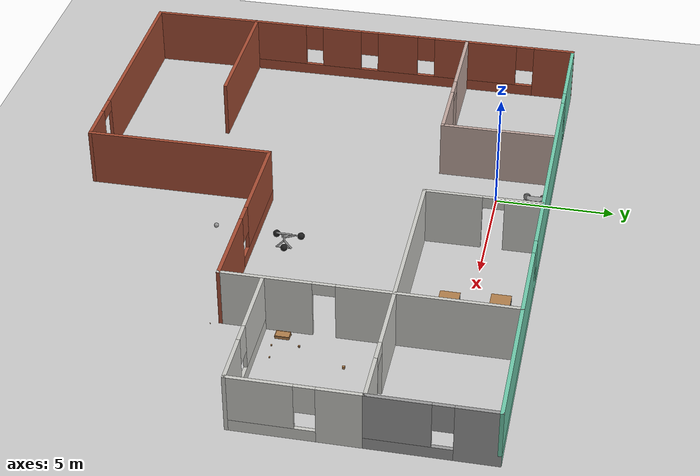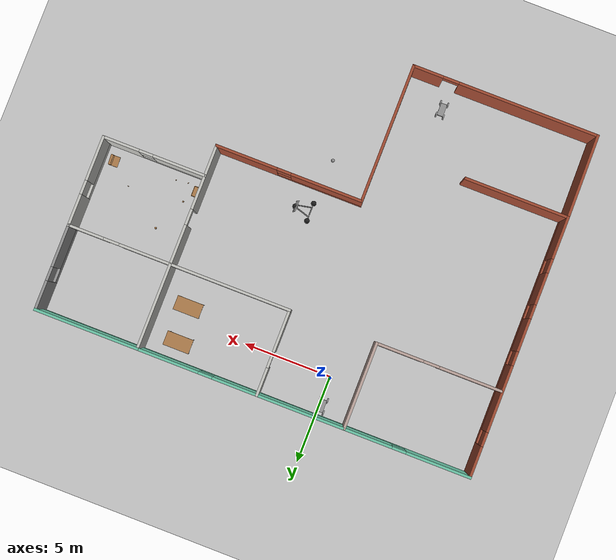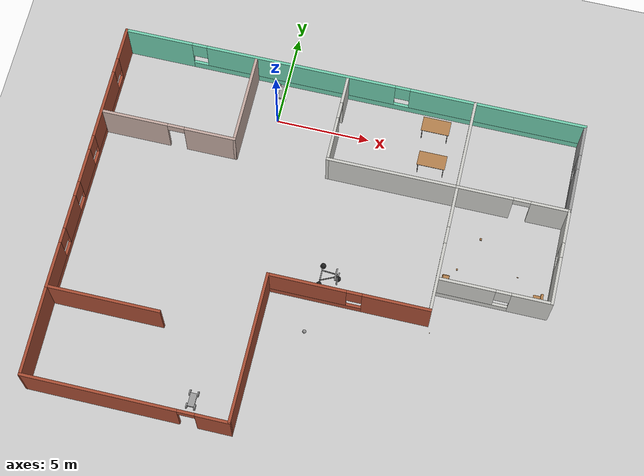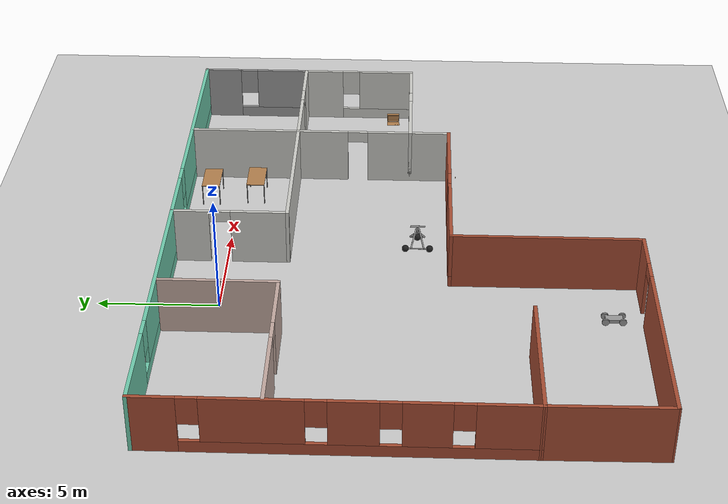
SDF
<sdf version="1.6">
 <world name="default">
  <plugin name="hello" filename="libhello.so"/>
  <light name="sun" type="directional">
   <pose>0 0 10 0 -0 0</pose>
   <diffuse>0.8 0.8 0.8 1</diffuse>
   <specular>0.2 0.2 0.2 1</specular>
   <attenuation>
    <range>1000</range>
    <constant>0.9</constant>
    <linear>0.01</linear>
    <quadratic>0.001</quadratic>
   </attenuation>
   <direction>-0.5 0.1 -0.9</direction>
  </light>
  <model name="ground_plane">
   <static>1</static>
   <link name="link">
    <collision name="collision">
     <geometry><plane><normal>0 0 1</normal><size>100 100</size></plane></geometry>
     <surface>
      <contact><collide_bitmask>65535</collide_bitmask></contact>
      <friction><ode><mu>100</mu><mu2>50</mu2></ode></friction>
     </surface>
    </collision>
    <visual name="visual">
     <cast_shadows>0</cast_shadows>
     <geometry><plane><normal>0 0 1</normal><size>100 100</size></plane></geometry>
     <material>
      <script><uri>file://media/materials/scripts/gazebo.material</uri><name>Gazebo/Grey</name></script>
     </material>
    </visual>
   </link>
  </model>
  <gravity>0 0 -9.8</gravity>
  <magnetic_field>6e-06 2.3e-05 -4.2e-05</magnetic_field>
  <atmosphere type="adiabatic"/>
  <physics name="default_physics" default="0" type="ode">
   <max_step_size>0.001</max_step_size>
   <real_time_factor>1</real_time_factor>
   <real_time_update_rate>1000</real_time_update_rate>
  </physics>
  <scene><ambient>0.4 0.4 0.4 1</ambient><background>0.7 0.7 0.7 1</background><shadows>1</shadows></scene>
  <spherical_coordinates>
   <surface_model>EARTH_WGS84</surface_model>
   <latitude_deg>0</latitude_deg>
   <longitude_deg>0</longitude_deg>
   <elevation>0</elevation>
   <heading_deg>0</heading_deg>
  </spherical_coordinates>
  <model name="house">
   <pose>3.5945 -7.51988 0 0 -0 0</pose>
   <link name="Wall_0">
    <pose>-12.4247 2.34692 0 0 0 -1.5708</pose>
    <visual name="Wall_0_Visual_0">
     <pose>-6.57999 0 1.25 0 -0 0</pose>
     <geometry><box><size>1.84003 0.15 2.5</size></box></geometry>
     <material>
      <script><uri>file://media/materials/scripts/gazebo.material</uri><name>Gazebo/Bricks</name></script>
      <ambient>1 1 1 1</ambient>
     </material>
     <meta><layer>0</layer></meta>
    </visual>
    <collision name="Wall_0_Collision_0">
     <geometry><box><size>1.84003 0.15 2.5</size></box></geometry>
     <pose>-6.57999 0 1.25 0 -0 0</pose>
    </collision>
    <visual name="Wall_0_Visual_1">
     <pose>0.920014 0 0.25 0 -0 0</pose>
     <geometry><box><size>13.16 0.15 0.5</size></box></geometry>
     <material>
      <script><uri>file://media/materials/scripts/gazebo.material</uri><name>Gazebo/Bricks</name></script>
      <ambient>1 1 1 1</ambient>
     </material>
     <meta><layer>0</layer></meta>
    </visual>
    <collision name="Wall_0_Collision_1">
     <geometry><box><size>13.16 0.15 0.5</size></box></geometry>
     <pose>0.920014 0 0.25 0 -0 0</pose>
    </collision>
    <visual name="Wall_0_Visual_2">
     <pose>-2.95937 0 1.5 0 -0 0</pose>
     <geometry><box><size>3.80122 0.15 2</size></box></geometry>
     <material>
      <script><uri>file://media/materials/scripts/gazebo.material</uri><name>Gazebo/Bricks</name></script>
      <ambient>1 1 1 1</ambient>
     </material>
     <meta><layer>0</layer></meta>
    </visual>
    <collision name="Wall_0_Collision_2">
     <geometry><box><size>3.80122 0.15 2</size></box></geometry>
     <pose>-2.95937 0 1.5 0 -0 0</pose>
    </collision>
    <visual name="Wall_0_Visual_3">
     <pose>0.678805 0 1.5 0 -0 0</pose>
     <geometry><box><size>1.87512 0.15 2</size></box></geometry>
     <material>
      <script><uri>file://media/materials/scripts/gazebo.material</uri><name>Gazebo/Bricks</name></script>
      <ambient>1 1 1 1</ambient>
     </material>
     <meta><layer>0</layer></meta>
    </visual>
    <collision name="Wall_0_Collision_3">
     <geometry><box><size>1.87512 0.15 2</size></box></geometry>
     <pose>0.678805 0 1.5 0 -0 0</pose>
    </collision>
    <visual name="Wall_0_Visual_4">
     <pose>3.32718 0 1.5 0 -0 0</pose>
     <geometry><box><size>1.82162 0.15 2</size></box></geometry>
     <material>
      <script><uri>file://media/materials/scripts/gazebo.material</uri><name>Gazebo/Bricks</name></script>
      <ambient>1 1 1 1</ambient>
     </material>
     <meta><layer>0</layer></meta>
    </visual>
    <collision name="Wall_0_Collision_4">
     <geometry><box><size>1.82162 0.15 2</size></box></geometry>
     <pose>3.32718 0 1.5 0 -0 0</pose>
    </collision>
    <visual name="Wall_0_Visual_5">
     <pose>6.269 0 1.5 0 -0 0</pose>
     <geometry><box><size>2.46201 0.15 2</size></box></geometry>
     <material>
      <script><uri>file://media/materials/scripts/gazebo.material</uri><name>Gazebo/Bricks</name></script>
      <ambient>1 1 1 1</ambient>
     </material>
     <meta><layer>0</layer></meta>
    </visual>
    <collision name="Wall_0_Collision_5">
     <geometry><box><size>2.46201 0.15 2</size></box></geometry>
     <pose>6.269 0 1.5 0 -0 0</pose>
    </collision>
    <visual name="Wall_0_Visual_6">
     <pose>-5.25997 0 1.9 0 -0 0</pose>
     <geometry><box><size>0.8 0.15 1.2</size></box></geometry>
     <material>
      <script><uri>file://media/materials/scripts/gazebo.material</uri><name>Gazebo/Bricks</name></script>
      <ambient>1 1 1 1</ambient>
     </material>
     <meta><layer>0</layer></meta>
    </visual>
    <collision name="Wall_0_Collision_6">
     <geometry><box><size>0.8 0.15 1.2</size></box></geometry>
     <pose>-5.25997 0 1.9 0 -0 0</pose>
    </collision>
    <visual name="Wall_0_Visual_7">
     <pose>-0.658757 0 1.9 0 -0 0</pose>
     <geometry><box><size>0.8 0.15 1.2</size></box></geometry>
     <material>
      <script><uri>file://media/materials/scripts/gazebo.material</uri><name>Gazebo/Bricks</name></script>
      <ambient>1 1 1 1</ambient>
     </material>
     <meta><layer>0</layer></meta>
    </visual>
    <collision name="Wall_0_Collision_7">
     <geometry><box><size>0.8 0.15 1.2</size></box></geometry>
     <pose>-0.658757 0 1.9 0 -0 0</pose>
    </collision>
    <visual name="Wall_0_Visual_8">
     <pose>2.01637 0 1.9 0 -0 0</pose>
     <geometry><box><size>0.8 0.15 1.2</size></box></geometry>
     <material>
      <script><uri>file://media/materials/scripts/gazebo.material</uri><name>Gazebo/Bricks</name></script>
      <ambient>1 1 1 1</ambient>
     </material>
     <meta><layer>0</layer></meta>
    </visual>
    <collision name="Wall_0_Collision_8">
     <geometry><box><size>0.8 0.15 1.2</size></box></geometry>
     <pose>2.01637 0 1.9 0 -0 0</pose>
    </collision>
    <visual name="Wall_0_Visual_9">
     <pose>4.63799 0 1.9 0 -0 0</pose>
     <geometry><box><size>0.8 0.15 1.2</size></box></geometry>
     <material>
      <script><uri>file://media/materials/scripts/gazebo.material</uri><name>Gazebo/Bricks</name></script>
      <ambient>1 1 1 1</ambient>
     </material>
     <meta><layer>0</layer></meta>
    </visual>
    <collision name="Wall_0_Collision_9">
     <geometry><box><size>0.8 0.15 1.2</size></box></geometry>
     <pose>4.63799 0 1.9 0 -0 0</pose>
    </collision>
   </link>
   <link name="Wall_10">
    <pose>9.5005 -0.178123 0 0 -0 3.14159</pose>
    <visual name="Wall_10_Visual_0">
     <pose>-1.93126 0 1.25 0 -0 0</pose>
     <geometry><box><size>2.13747 0.15 2.5</size></box></geometry>
     <material>
      <script><uri>file://media/materials/scripts/gazebo.material</uri><name>Gazebo/CeilingTiled</name></script>
      <ambient>1 1 1 1</ambient>
     </material>
     <meta><layer>0</layer></meta>
    </visual>
    <collision name="Wall_10_Collision_0">
     <geometry><box><size>2.13747 0.15 2.5</size></box></geometry>
     <pose>-1.93126 0 1.25 0 -0 0</pose>
    </collision>
    <visual name="Wall_10_Visual_1">
     <pose>1.06874 0 0.25 0 -0 0</pose>
     <geometry><box><size>3.86253 0.15 0.5</size></box></geometry>
     <material>
      <script><uri>file://media/materials/scripts/gazebo.material</uri><name>Gazebo/CeilingTiled</name></script>
      <ambient>1 1 1 1</ambient>
     </material>
     <meta><layer>0</layer></meta>
    </visual>
    <collision name="Wall_10_Collision_1">
     <geometry><box><size>3.86253 0.15 0.5</size></box></geometry>
     <pose>1.06874 0 0.25 0 -0 0</pose>
    </collision>
    <visual name="Wall_10_Visual_2">
     <pose>1.46874 0 1.5 0 -0 0</pose>
     <geometry><box><size>3.06253 0.15 2</size></box></geometry>
     <material>
      <script><uri>file://media/materials/scripts/gazebo.material</uri><name>Gazebo/CeilingTiled</name></script>
      <ambient>1 1 1 1</ambient>
     </material>
     <meta><layer>0</layer></meta>
    </visual>
    <collision name="Wall_10_Collision_2">
     <geometry><box><size>3.06253 0.15 2</size></box></geometry>
     <pose>1.46874 0 1.5 0 -0 0</pose>
    </collision>
    <visual name="Wall_10_Visual_3">
     <pose>-0.462526 0 1.9 0 -0 0</pose>
     <geometry><box><size>0.8 0.15 1.2</size></box></geometry>
     <material>
      <script><uri>file://media/materials/scripts/gazebo.material</uri><name>Gazebo/CeilingTiled</name></script>
      <ambient>1 1 1 1</ambient>
     </material>
     <meta><layer>0</layer></meta>
    </visual>
    <collision name="Wall_10_Collision_3">
     <geometry><box><size>0.8 0.15 1.2</size></box></geometry>
     <pose>-0.462526 0 1.9 0 -0 0</pose>
    </collision>
   </link>
   <link name="Wall_12">
    <pose>2.4005 -1.92112 0 0 -0 3.14159</pose>
    <visual name="Wall_12_Visual_0">
     <pose>-2.46809 0 1.25 0 -0 0</pose>
     <geometry><box><size>3.56381 0.15 2.5</size></box></geometry>
     <material>
      <script><uri>file://media/materials/scripts/gazebo.material</uri><name>Gazebo/Bricks</name></script>
      <ambient>1 1 1 1</ambient>
     </material>
     <meta><layer>0</layer></meta>
    </visual>
    <collision name="Wall_12_Collision_0">
     <geometry><box><size>3.56381 0.15 2.5</size></box></geometry>
     <pose>-2.46809 0 1.25 0 -0 0</pose>
    </collision>
    <visual name="Wall_12_Visual_1">
     <pose>1.78191 0 0.25 0 -0 0</pose>
     <geometry><box><size>4.93619 0.15 0.5</size></box></geometry>
     <material>
      <script><uri>file://media/materials/scripts/gazebo.material</uri><name>Gazebo/Bricks</name></script>
      <ambient>1 1 1 1</ambient>
     </material>
     <meta><layer>0</layer></meta>
    </visual>
    <collision name="Wall_12_Collision_1">
     <geometry><box><size>4.93619 0.15 0.5</size></box></geometry>
     <pose>1.78191 0 0.25 0 -0 0</pose>
    </collision>
    <visual name="Wall_12_Visual_2">
     <pose>2.18191 0 1.5 0 -0 0</pose>
     <geometry><box><size>4.13619 0.15 2</size></box></geometry>
     <material>
      <script><uri>file://media/materials/scripts/gazebo.material</uri><name>Gazebo/Bricks</name></script>
      <ambient>1 1 1 1</ambient>
     </material>
     <meta><layer>0</layer></meta>
    </visual>
    <collision name="Wall_12_Collision_2">
     <geometry><box><size>4.13619 0.15 2</size></box></geometry>
     <pose>2.18191 0 1.5 0 -0 0</pose>
    </collision>
    <visual name="Wall_12_Visual_3">
     <pose>-0.286187 0 1.9 0 -0 0</pose>
     <geometry><box><size>0.8 0.15 1.2</size></box></geometry>
     <material>
      <script><uri>file://media/materials/scripts/gazebo.material</uri><name>Gazebo/Bricks</name></script>
      <ambient>1 1 1 1</ambient>
     </material>
     <meta><layer>0</layer></meta>
    </visual>
    <collision name="Wall_12_Collision_3">
     <geometry><box><size>0.8 0.15 1.2</size></box></geometry>
     <pose>-0.286187 0 1.9 0 -0 0</pose>
    </collision>
   </link>
   <link name="Wall_13">
    <collision name="Wall_13_Collision">
     <geometry><box><size>8 0.15 2.5</size></box></geometry>
     <pose>0 0 1.25 0 -0 0</pose>
    </collision>
    <visual name="Wall_13_Visual">
     <pose>0 0 1.25 0 -0 0</pose>
     <geometry><box><size>8 0.15 2.5</size></box></geometry>
     <material>
      <script><uri>file://media/materials/scripts/gazebo.material</uri><name>Gazebo/Bricks</name></script>
      <ambient>1 1 1 1</ambient>
     </material>
     <meta><layer>0</layer></meta>
    </visual>
    <pose>-1.7745 -5.84612 0 0 0 -1.5708</pose>
   </link>
   <link name="Wall_14">
    <pose>-7.0745 -9.77112 0 0 -0 3.14159</pose>
    <visual name="Wall_14_Visual_0">
     <pose>-4.47594 0 1.25 0 -0 0</pose>
     <geometry><box><size>1.79812 0.15 2.5</size></box></geometry>
     <material>
      <script><uri>file://media/materials/scripts/gazebo.material</uri><name>Gazebo/Bricks</name></script>
      <ambient>1 1 1 1</ambient>
     </material>
     <meta><layer>0</layer></meta>
    </visual>
    <collision name="Wall_14_Collision_0">
     <geometry><box><size>1.79812 0.15 2.5</size></box></geometry>
     <pose>-4.47594 0 1.25 0 -0 0</pose>
    </collision>
    <visual name="Wall_14_Visual_1">
     <pose>1.34906 0 1.25 0 -0 0</pose>
     <geometry><box><size>8.05188 0.15 2.5</size></box></geometry>
     <material>
      <script><uri>file://media/materials/scripts/gazebo.material</uri><name>Gazebo/Bricks</name></script>
      <ambient>1 1 1 1</ambient>
     </material>
     <meta><layer>0</layer></meta>
    </visual>
    <collision name="Wall_14_Collision_1">
     <geometry><box><size>8.05188 0.15 2.5</size></box></geometry>
     <pose>1.34906 0 1.25 0 -0 0</pose>
    </collision>
    <visual name="Wall_14_Visual_2">
     <pose>-3.12688 0 2.25 0 -0 0</pose>
     <geometry><box><size>0.9 0.15 0.5</size></box></geometry>
     <material>
      <script><uri>file://media/materials/scripts/gazebo.material</uri><name>Gazebo/Bricks</name></script>
      <ambient>1 1 1 1</ambient>
     </material>
     <meta><layer>0</layer></meta>
    </visual>
    <collision name="Wall_14_Collision_2">
     <geometry><box><size>0.9 0.15 0.5</size></box></geometry>
     <pose>-3.12688 0 2.25 0 -0 0</pose>
    </collision>
   </link>
   <link name="Wall_15">
    <collision name="Wall_15_Collision">
     <geometry><box><size>4.84331 0.15 2.5</size></box></geometry>
     <pose>0 0 1.25 0 -0 0</pose>
    </collision>
    <visual name="Wall_15_Visual">
     <pose>0 0 1.25 0 -0 0</pose>
     <geometry><box><size>4.84331 0.15 2.5</size></box></geometry>
     <material>
      <script><uri>file://media/materials/scripts/gazebo.material</uri><name>Gazebo/Bricks</name></script>
      <ambient>1 1 1 1</ambient>
     </material>
     <meta><layer>0</layer></meta>
    </visual>
    <pose>-12.3996 -7.4246 0 0 -0 1.58149</pose>
   </link>
   <link name="Wall_16">
    <collision name="Wall_16_Collision">
     <geometry><box><size>6 0.15 2.5</size></box></geometry>
     <pose>0 0 1.25 0 -0 0</pose>
    </collision>
    <visual name="Wall_16_Visual">
     <pose>0 0 1.25 0 -0 0</pose>
     <geometry><box><size>6 0.15 2.5</size></box></geometry>
     <material>
      <script><uri>file://media/materials/scripts/gazebo.material</uri><name>Gazebo/Bricks</name></script>
      <ambient>1 1 1 1</ambient>
     </material>
     <meta><layer>0</layer></meta>
    </visual>
    <pose>-9.4997 -5.07808 0 0 -0 0</pose>
   </link>
   <link name="Wall_18">
    <pose>-8.80439 4.8949 0 0 -0 0</pose>
    <visual name="Wall_18_Visual_0">
     <pose>-1.82947 0 1.25 0 -0 0</pose>
     <geometry><box><size>3.59105 0.15 2.5</size></box></geometry>
     <material>
      <script><uri>file://media/materials/scripts/gazebo.material</uri><name>Gazebo/Grey</name></script>
      <ambient>0.760784 0.662745 0.627451 1</ambient>
     </material>
     <meta><layer>0</layer></meta>
    </visual>
    <collision name="Wall_18_Collision_0">
     <geometry><box><size>3.59105 0.15 2.5</size></box></geometry>
     <pose>-1.82947 0 1.25 0 -0 0</pose>
    </collision>
    <visual name="Wall_18_Visual_1">
     <pose>2.24553 0 1.25 0 -0 0</pose>
     <geometry><box><size>2.75895 0.15 2.5</size></box></geometry>
     <material>
      <script><uri>file://media/materials/scripts/gazebo.material</uri><name>Gazebo/Grey</name></script>
      <ambient>0.760784 0.662745 0.627451 1</ambient>
     </material>
     <meta><layer>0</layer></meta>
    </visual>
    <collision name="Wall_18_Collision_1">
     <geometry><box><size>2.75895 0.15 2.5</size></box></geometry>
     <pose>2.24553 0 1.25 0 -0 0</pose>
    </collision>
    <visual name="Wall_18_Visual_2">
     <pose>0.416054 0 2.25 0 -0 0</pose>
     <geometry><box><size>0.9 0.15 0.5</size></box></geometry>
     <material>
      <script><uri>file://media/materials/scripts/gazebo.material</uri><name>Gazebo/Grey</name></script>
      <ambient>0.760784 0.662745 0.627451 1</ambient>
     </material>
     <meta><layer>0</layer></meta>
    </visual>
    <collision name="Wall_18_Collision_2">
     <geometry><box><size>0.9 0.15 0.5</size></box></geometry>
     <pose>0.416054 0 2.25 0 -0 0</pose>
    </collision>
   </link>
   <link name="Wall_21">
    <collision name="Wall_21_Collision">
     <geometry><box><size>5 0.15 2.5</size></box></geometry>
     <pose>0 0 1.25 0 -0 0</pose>
    </collision>
    <visual name="Wall_21_Visual">
     <pose>0 0 1.25 0 -0 0</pose>
     <geometry><box><size>5 0.15 2.5</size></box></geometry>
     <material>
      <script><uri>file://media/materials/scripts/gazebo.material</uri><name>Gazebo/Grey</name></script>
      <ambient>0.760784 0.662745 0.627451 1</ambient>
     </material>
     <meta><layer>0</layer></meta>
    </visual>
    <pose>-5.25439 7.3199 0 0 -0 1.5708</pose>
   </link>
   <link name="Wall_23">
    <collision name="Wall_23_Collision">
     <geometry><box><size>5 0.15 2.5</size></box></geometry>
     <pose>0 0 1.25 0 -0 0</pose>
    </collision>
    <visual name="Wall_23_Visual">
     <pose>0 0 1.25 0 -0 0</pose>
     <geometry><box><size>5 0.15 2.5</size></box></geometry>
     <material>
      <script><uri>file://media/materials/scripts/gazebo.material</uri><name>Gazebo/CeilingTiled</name></script>
      <ambient>1 1 1 1</ambient>
     </material>
     <meta><layer>0</layer></meta>
    </visual>
    <pose>6.5755 7.34688 0 0 -0 1.5708</pose>
   </link>
   <link name="Wall_25">
    <collision name="Wall_25_Collision">
     <geometry><box><size>7 0.15 2.5</size></box></geometry>
     <pose>0 0 1.25 0 -0 0</pose>
    </collision>
    <visual name="Wall_25_Visual">
     <pose>0 0 1.25 0 -0 0</pose>
     <geometry><box><size>7 0.15 2.5</size></box></geometry>
     <material>
      <script><uri>file://media/materials/scripts/gazebo.material</uri><name>Gazebo/CeilingTiled</name></script>
      <ambient>1 1 1 1</ambient>
     </material>
     <meta><layer>0</layer></meta>
    </visual>
    <pose>3.1505 4.92188 0 0 -0 3.14159</pose>
   </link>
   <link name="Wall_26">
    <pose>-0.274503 7.34688 0 0 -0 1.5708</pose>
    <visual name="Wall_26_Visual_0">
     <pose>-1.26474 0 1.25 0 -0 0</pose>
     <geometry><box><size>2.47052 0.15 2.5</size></box></geometry>
     <material>
      <script><uri>file://media/materials/scripts/gazebo.material</uri><name>Gazebo/CeilingTiled</name></script>
      <ambient>1 1 1 1</ambient>
     </material>
     <meta><layer>0</layer></meta>
    </visual>
    <collision name="Wall_26_Collision_0">
     <geometry><box><size>2.47052 0.15 2.5</size></box></geometry>
     <pose>-1.26474 0 1.25 0 -0 0</pose>
    </collision>
    <visual name="Wall_26_Visual_1">
     <pose>1.68526 0 1.25 0 -0 0</pose>
     <geometry><box><size>1.62948 0.15 2.5</size></box></geometry>
     <material>
      <script><uri>file://media/materials/scripts/gazebo.material</uri><name>Gazebo/CeilingTiled</name></script>
      <ambient>1 1 1 1</ambient>
     </material>
     <meta><layer>0</layer></meta>
    </visual>
    <collision name="Wall_26_Collision_1">
     <geometry><box><size>1.62948 0.15 2.5</size></box></geometry>
     <pose>1.68526 0 1.25 0 -0 0</pose>
    </collision>
    <visual name="Wall_26_Visual_2">
     <pose>0.420524 0 2.25 0 -0 0</pose>
     <geometry><box><size>0.9 0.15 0.5</size></box></geometry>
     <material>
      <script><uri>file://media/materials/scripts/gazebo.material</uri><name>Gazebo/CeilingTiled</name></script>
      <ambient>1 1 1 1</ambient>
     </material>
     <meta><layer>0</layer></meta>
    </visual>
    <collision name="Wall_26_Collision_2">
     <geometry><box><size>0.9 0.15 0.5</size></box></geometry>
     <pose>0.420524 0 2.25 0 -0 0</pose>
    </collision>
   </link>
   <link name="Wall_28">
    <pose>9.5005 4.92188 0 0 -0 0</pose>
    <visual name="Wall_28_Visual_0">
     <pose>-1.49374 0 1.25 0 -0 0</pose>
     <geometry><box><size>3.01253 0.15 2.5</size></box></geometry>
     <material>
      <script><uri>file://media/materials/scripts/gazebo.material</uri><name>Gazebo/CeilingTiled</name></script>
      <ambient>1 1 1 1</ambient>
     </material>
     <meta><layer>0</layer></meta>
    </visual>
    <collision name="Wall_28_Collision_0">
     <geometry><box><size>3.01253 0.15 2.5</size></box></geometry>
     <pose>-1.49374 0 1.25 0 -0 0</pose>
    </collision>
    <visual name="Wall_28_Visual_1">
     <pose>1.95626 0 1.25 0 -0 0</pose>
     <geometry><box><size>2.08747 0.15 2.5</size></box></geometry>
     <material>
      <script><uri>file://media/materials/scripts/gazebo.material</uri><name>Gazebo/CeilingTiled</name></script>
      <ambient>1 1 1 1</ambient>
     </material>
     <meta><layer>0</layer></meta>
    </visual>
    <collision name="Wall_28_Collision_1">
     <geometry><box><size>2.08747 0.15 2.5</size></box></geometry>
     <pose>1.95626 0 1.25 0 -0 0</pose>
    </collision>
    <visual name="Wall_28_Visual_2">
     <pose>0.462526 0 2.25 0 -0 0</pose>
     <geometry><box><size>0.9 0.15 0.5</size></box></geometry>
     <material>
      <script><uri>file://media/materials/scripts/gazebo.material</uri><name>Gazebo/CeilingTiled</name></script>
      <ambient>1 1 1 1</ambient>
     </material>
     <meta><layer>0</layer></meta>
    </visual>
    <collision name="Wall_28_Collision_2">
     <geometry><box><size>0.9 0.15 0.5</size></box></geometry>
     <pose>0.462526 0 2.25 0 -0 0</pose>
    </collision>
   </link>
   <link name="Wall_3">
    <pose>0.000298 9.77192 0 0 -0 0</pose>
    <visual name="Wall_3_Visual_0">
     <pose>-10.6443 0 1.25 0 -0 0</pose>
     <geometry><box><size>3.71137 0.15 2.5</size></box></geometry>
     <material>
      <script><uri>file://media/materials/scripts/gazebo.material</uri><name>Gazebo/Grey</name></script>
      <ambient>0.435294 0.796078 0.67451 1</ambient>
     </material>
     <meta><layer>0</layer></meta>
    </visual>
    <collision name="Wall_3_Collision_0">
     <geometry><box><size>3.71137 0.15 2.5</size></box></geometry>
     <pose>-10.6443 0 1.25 0 -0 0</pose>
    </collision>
    <visual name="Wall_3_Visual_1">
     <pose>1.85568 0 0.25 0 -0 0</pose>
     <geometry><box><size>21.2886 0.15 0.5</size></box></geometry>
     <material>
      <script><uri>file://media/materials/scripts/gazebo.material</uri><name>Gazebo/Grey</name></script>
      <ambient>0.435294 0.796078 0.67451 1</ambient>
     </material>
     <meta><layer>0</layer></meta>
    </visual>
    <collision name="Wall_3_Collision_1">
     <geometry><box><size>21.2886 0.15 0.5</size></box></geometry>
     <pose>1.85568 0 0.25 0 -0 0</pose>
    </collision>
    <visual name="Wall_3_Visual_2">
     <pose>-2.85112 0 1.5 0 -0 0</pose>
     <geometry><box><size>10.275 0.15 2</size></box></geometry>
     <material>
      <script><uri>file://media/materials/scripts/gazebo.material</uri><name>Gazebo/Grey</name></script>
      <ambient>0.435294 0.796078 0.67451 1</ambient>
     </material>
     <meta><layer>0</layer></meta>
    </visual>
    <collision name="Wall_3_Collision_2">
     <geometry><box><size>10.275 0.15 2</size></box></geometry>
     <pose>-2.85112 0 1.5 0 -0 0</pose>
    </collision>
    <visual name="Wall_3_Visual_3">
     <pose>7.79319 0 1.5 0 -0 0</pose>
     <geometry><box><size>9.41362 0.15 2</size></box></geometry>
     <material>
      <script><uri>file://media/materials/scripts/gazebo.material</uri><name>Gazebo/Grey</name></script>
      <ambient>0.435294 0.796078 0.67451 1</ambient>
     </material>
     <meta><layer>0</layer></meta>
    </visual>
    <collision name="Wall_3_Collision_3">
     <geometry><box><size>9.41362 0.15 2</size></box></geometry>
     <pose>7.79319 0 1.5 0 -0 0</pose>
    </collision>
    <visual name="Wall_3_Visual_4">
     <pose>-8.38863 0 1.9 0 -0 0</pose>
     <geometry><box><size>0.8 0.15 1.2</size></box></geometry>
     <material>
      <script><uri>file://media/materials/scripts/gazebo.material</uri><name>Gazebo/Grey</name></script>
      <ambient>0.435294 0.796078 0.67451 1</ambient>
     </material>
     <meta><layer>0</layer></meta>
    </visual>
    <collision name="Wall_3_Collision_4">
     <geometry><box><size>0.8 0.15 1.2</size></box></geometry>
     <pose>-8.38863 0 1.9 0 -0 0</pose>
    </collision>
    <visual name="Wall_3_Visual_5">
     <pose>2.68639 0 1.9 0 -0 0</pose>
     <geometry><box><size>0.8 0.15 1.2</size></box></geometry>
     <material>
      <script><uri>file://media/materials/scripts/gazebo.material</uri><name>Gazebo/Grey</name></script>
      <ambient>0.435294 0.796078 0.67451 1</ambient>
     </material>
     <meta><layer>0</layer></meta>
    </visual>
    <collision name="Wall_3_Collision_5">
     <geometry><box><size>0.8 0.15 1.2</size></box></geometry>
     <pose>2.68639 0 1.9 0 -0 0</pose>
    </collision>
   </link>
   <link name="Wall_5">
    <pose>12.4254 7.3469 0 0 0 -1.57075</pose>
    <visual name="Wall_5_Visual_0">
     <pose>-1.6335 0 1.25 0 -0 0</pose>
     <geometry><box><size>1.73299 0.15 2.5</size></box></geometry>
     <material>
      <script><uri>file://media/materials/scripts/gazebo.material</uri><name>Gazebo/Grey</name></script>
      <ambient>1 1 1 1</ambient>
     </material>
     <meta><layer>0</layer></meta>
    </visual>
    <collision name="Wall_5_Collision_0">
     <geometry><box><size>1.73299 0.15 2.5</size></box></geometry>
     <pose>-1.6335 0 1.25 0 -0 0</pose>
    </collision>
    <visual name="Wall_5_Visual_1">
     <pose>0.866497 0 0.25 0 -0 0</pose>
     <geometry><box><size>3.26701 0.15 0.5</size></box></geometry>
     <material>
      <script><uri>file://media/materials/scripts/gazebo.material</uri><name>Gazebo/Grey</name></script>
      <ambient>1 1 1 1</ambient>
     </material>
     <meta><layer>0</layer></meta>
    </visual>
    <collision name="Wall_5_Collision_1">
     <geometry><box><size>3.26701 0.15 0.5</size></box></geometry>
     <pose>0.866497 0 0.25 0 -0 0</pose>
    </collision>
    <visual name="Wall_5_Visual_2">
     <pose>1.2665 0 1.5 0 -0 0</pose>
     <geometry><box><size>2.46701 0.15 2</size></box></geometry>
     <material>
      <script><uri>file://media/materials/scripts/gazebo.material</uri><name>Gazebo/Grey</name></script>
      <ambient>1 1 1 1</ambient>
     </material>
     <meta><layer>0</layer></meta>
    </visual>
    <collision name="Wall_5_Collision_2">
     <geometry><box><size>2.46701 0.15 2</size></box></geometry>
     <pose>1.2665 0 1.5 0 -0 0</pose>
    </collision>
    <visual name="Wall_5_Visual_3">
     <pose>-0.367006 0 1.9 0 -0 0</pose>
     <geometry><box><size>0.8 0.15 1.2</size></box></geometry>
     <material>
      <script><uri>file://media/materials/scripts/gazebo.material</uri><name>Gazebo/Grey</name></script>
      <ambient>1 1 1 1</ambient>
     </material>
     <meta><layer>0</layer></meta>
    </visual>
    <collision name="Wall_5_Collision_3">
     <geometry><box><size>0.8 0.15 1.2</size></box></geometry>
     <pose>-0.367006 0 1.9 0 -0 0</pose>
    </collision>
   </link>
   <link name="Wall_7">
    <pose>6.5755 1.50038 0 0 0 -1.5708</pose>
    <visual name="Wall_7_Visual_0">
     <pose>-2.32463 0 1.25 0 -0 0</pose>
     <geometry><box><size>2.34374 0.15 2.5</size></box></geometry>
     <material>
      <script><uri>file://media/materials/scripts/gazebo.material</uri><name>Gazebo/CeilingTiled</name></script>
      <ambient>1 1 1 1</ambient>
     </material>
     <meta><layer>0</layer></meta>
    </visual>
    <collision name="Wall_7_Collision_0">
     <geometry><box><size>2.34374 0.15 2.5</size></box></geometry>
     <pose>-2.32463 0 1.25 0 -0 0</pose>
    </collision>
    <visual name="Wall_7_Visual_1">
     <pose>1.62187 0 1.25 0 -0 0</pose>
     <geometry><box><size>3.74926 0.15 2.5</size></box></geometry>
     <material>
      <script><uri>file://media/materials/scripts/gazebo.material</uri><name>Gazebo/CeilingTiled</name></script>
      <ambient>1 1 1 1</ambient>
     </material>
     <meta><layer>0</layer></meta>
    </visual>
    <collision name="Wall_7_Collision_1">
     <geometry><box><size>3.74926 0.15 2.5</size></box></geometry>
     <pose>1.62187 0 1.25 0 -0 0</pose>
    </collision>
    <visual name="Wall_7_Visual_2">
     <pose>-0.702764 0 2.25 0 -0 0</pose>
     <geometry><box><size>0.9 0.15 0.5</size></box></geometry>
     <material>
      <script><uri>file://media/materials/scripts/gazebo.material</uri><name>Gazebo/CeilingTiled</name></script>
      <ambient>1 1 1 1</ambient>
     </material>
     <meta><layer>0</layer></meta>
    </visual>
    <collision name="Wall_7_Collision_2">
     <geometry><box><size>0.9 0.15 0.5</size></box></geometry>
     <pose>-0.702764 0 2.25 0 -0 0</pose>
    </collision>
   </link>
   <link name="Wall_9">
    <pose>12.4255 2.37188 0 0 0 -1.5708</pose>
    <visual name="Wall_9_Visual_0">
     <pose>-1.69564 0 1.25 0 -0 0</pose>
     <geometry><box><size>1.85871 0.15 2.5</size></box></geometry>
     <material>
      <script><uri>file://media/materials/scripts/gazebo.material</uri><name>Gazebo/CeilingTiled</name></script>
      <ambient>1 1 1 1</ambient>
     </material>
     <meta><layer>0</layer></meta>
    </visual>
    <collision name="Wall_9_Collision_0">
     <geometry><box><size>1.85871 0.15 2.5</size></box></geometry>
     <pose>-1.69564 0 1.25 0 -0 0</pose>
    </collision>
    <visual name="Wall_9_Visual_1">
     <pose>0.929356 0 0.25 0 -0 0</pose>
     <geometry><box><size>3.39129 0.15 0.5</size></box></geometry>
     <material>
      <script><uri>file://media/materials/scripts/gazebo.material</uri><name>Gazebo/CeilingTiled</name></script>
      <ambient>1 1 1 1</ambient>
     </material>
     <meta><layer>0</layer></meta>
    </visual>
    <collision name="Wall_9_Collision_1">
     <geometry><box><size>3.39129 0.15 0.5</size></box></geometry>
     <pose>0.929356 0 0.25 0 -0 0</pose>
    </collision>
    <visual name="Wall_9_Visual_2">
     <pose>1.32936 0 1.5 0 -0 0</pose>
     <geometry><box><size>2.59129 0.15 2</size></box></geometry>
     <material>
      <script><uri>file://media/materials/scripts/gazebo.material</uri><name>Gazebo/CeilingTiled</name></script>
      <ambient>1 1 1 1</ambient>
     </material>
     <meta><layer>0</layer></meta>
    </visual>
    <collision name="Wall_9_Collision_2">
     <geometry><box><size>2.59129 0.15 2</size></box></geometry>
     <pose>1.32936 0 1.5 0 -0 0</pose>
    </collision>
    <visual name="Wall_9_Visual_3">
     <pose>-0.366289 0 1.9 0 -0 0</pose>
     <geometry><box><size>0.8 0.15 1.2</size></box></geometry>
     <material>
      <script><uri>file://media/materials/scripts/gazebo.material</uri><name>Gazebo/CeilingTiled</name></script>
      <ambient>1 1 1 1</ambient>
     </material>
     <meta><layer>0</layer></meta>
    </visual>
    <collision name="Wall_9_Collision_3">
     <geometry><box><size>0.8 0.15 1.2</size></box></geometry>
     <pose>-0.366289 0 1.9 0 -0 0</pose>
    </collision>
   </link>
   <static>1</static>
  </model>
  <model name="wood_cube_10cm">
   <link name="link">
    <pose>0 0 0.05 0 -0 0</pose>
    <inertial>
     <mass>0.5167</mass>
     <inertia>
      <ixx>0.000861167</ixx>
      <ixy>0</ixy>
      <ixz>0</ixz>
      <iyy>0.000861167</iyy>
      <iyz>0</iyz>
      <izz>0.000861167</izz>
     </inertia>
    </inertial>
    <collision name="collision">
     <geometry><box><size>0.1 0.1 0.1</size></box></geometry>
     <surface>
      <contact>
       <poissons_ratio>0.347</poissons_ratio>
       <elastic_modulus>8.8e+09</elastic_modulus>
       <ode><kp>100000</kp><kd>100</kd><max_vel>100</max_vel><min_depth>0.001</min_depth></ode>
      </contact>
      <friction>
       <torsional>
        <coefficient>1</coefficient>
        <use_patch_radius>0</use_patch_radius>
        <surface_radius>0.01</surface_radius>
       </torsional>
      </friction>
     </surface>
    </collision>
    <visual name="visual">
     <geometry><box><size>0.1 0.1 0.1</size></box></geometry>
     <material>
      <script><uri>file://media/materials/scripts/gazebo.material</uri><name>Gazebo/Wood</name></script>
     </material>
    </visual>
   </link>
   <pose>11.9568 -4.2046 -0.001013 0 -0 0</pose>
  </model>
  <model name="wooden_peg">
   <link name="link">
    <pose>0 0 0.04 0 -0 0</pose>
    <inertial>
     <mass>0.0175</mass>
     <inertia>
      <ixx>9.74923e-06</ixx>
      <ixy>0</ixy>
      <ixz>0</ixz>
      <iyy>9.74923e-06</iyy>
      <iyz>0</iyz>
      <izz>8.31797e-07</izz>
     </inertia>
    </inertial>
    <collision name="collision">
     <geometry><cylinder><radius>0.00975</radius><length>0.08</length></cylinder></geometry>
     <surface>
      <contact>
       <poissons_ratio>0.347</poissons_ratio>
       <elastic_modulus>8.8e+09</elastic_modulus>
       <ode><kp>100000</kp><kd>100</kd><max_vel>100</max_vel><min_depth>0.001</min_depth></ode>
      </contact>
      <friction>
       <torsional>
        <coefficient>1</coefficient>
        <use_patch_radius>0</use_patch_radius>
        <surface_radius>0.01</surface_radius>
       </torsional>
      </friction>
     </surface>
    </collision>
    <visual name="visual">
     <geometry><cylinder><radius>0.00975</radius><length>0.08</length></cylinder></geometry>
     <material>
      <script><uri>file://media/materials/scripts/gazebo.material</uri><name>Gazebo/Wood</name></script>
     </material>
    </visual>
   </link>
   <pose>10.3731 -9.83148 -0.001 0 -0 0</pose>
  </model>
  <model name="table">
   <static>1</static>
   <link name="link">
    <collision name="surface">
     <pose>0 0 1 0 -0 0</pose>
     <geometry><box><size>1.5 0.8 0.03</size></box></geometry>
     <surface><friction><ode><mu>0.6</mu><mu2>0.6</mu2></ode></friction></surface>
    </collision>
    <visual name="visual1">
     <pose>0 0 1 0 -0 0</pose>
     <geometry><box><size>1.5 0.8 0.03</size></box></geometry>
     <material>
      <script><uri>file://media/materials/scripts/gazebo.material</uri><name>Gazebo/Wood</name></script>
     </material>
    </visual>
    <collision name="front_left_leg">
     <pose>0.68 0.38 0.5 0 -0 0</pose>
     <geometry><cylinder><radius>0.02</radius><length>1</length></cylinder></geometry>
    </collision>
    <visual name="front_left_leg">
     <pose>0.68 0.38 0.5 0 -0 0</pose>
     <geometry><cylinder><radius>0.02</radius><length>1</length></cylinder></geometry>
     <material>
      <script><uri>file://media/materials/scripts/gazebo.material</uri><name>Gazebo/Grey</name></script>
     </material>
    </visual>
    <collision name="front_right_leg">
     <pose>0.68 -0.38 0.5 0 -0 0</pose>
     <geometry><cylinder><radius>0.02</radius><length>1</length></cylinder></geometry>
    </collision>
    <visual name="front_right_leg">
     <pose>0.68 -0.38 0.5 0 -0 0</pose>
     <geometry><cylinder><radius>0.02</radius><length>1</length></cylinder></geometry>
     <material>
      <script><uri>file://media/materials/scripts/gazebo.material</uri><name>Gazebo/Grey</name></script>
     </material>
    </visual>
    <collision name="back_right_leg">
     <pose>-0.68 -0.38 0.5 0 -0 0</pose>
     <geometry><cylinder><radius>0.02</radius><length>1</length></cylinder></geometry>
    </collision>
    <visual name="back_right_leg">
     <pose>-0.68 -0.38 0.5 0 -0 0</pose>
     <geometry><cylinder><radius>0.02</radius><length>1</length></cylinder></geometry>
     <material>
      <script><uri>file://media/materials/scripts/gazebo.material</uri><name>Gazebo/Grey</name></script>
     </material>
    </visual>
    <collision name="back_left_leg">
     <pose>-0.68 0.38 0.5 0 -0 0</pose>
     <geometry><cylinder><radius>0.02</radius><length>1</length></cylinder></geometry>
    </collision>
    <visual name="back_left_leg">
     <pose>-0.68 0.38 0.5 0 -0 0</pose>
     <geometry><cylinder><radius>0.02</radius><length>1</length></cylinder></geometry>
     <material>
      <script><uri>file://media/materials/scripts/gazebo.material</uri><name>Gazebo/Grey</name></script>
     </material>
    </visual>
   </link>
   <pose>8.39393 1.19948 0 0 -0 0</pose>
  </model>
  <model name="table_0">
   <static>1</static>
   <link name="link">
    <collision name="surface">
     <pose>0 0 1 0 -0 0</pose>
     <geometry><box><size>1.5 0.8 0.03</size></box></geometry>
     <surface><friction><ode><mu>0.6</mu><mu2>0.6</mu2></ode></friction></surface>
    </collision>
    <visual name="visual1">
     <pose>0 0 1 0 -0 0</pose>
     <geometry><box><size>1.5 0.8 0.03</size></box></geometry>
     <material>
      <script><uri>file://media/materials/scripts/gazebo.material</uri><name>Gazebo/Wood</name></script>
     </material>
    </visual>
    <collision name="front_left_leg">
     <pose>0.68 0.38 0.5 0 -0 0</pose>
     <geometry><cylinder><radius>0.02</radius><length>1</length></cylinder></geometry>
    </collision>
    <visual name="front_left_leg">
     <pose>0.68 0.38 0.5 0 -0 0</pose>
     <geometry><cylinder><radius>0.02</radius><length>1</length></cylinder></geometry>
     <material>
      <script><uri>file://media/materials/scripts/gazebo.material</uri><name>Gazebo/Grey</name></script>
     </material>
    </visual>
    <collision name="front_right_leg">
     <pose>0.68 -0.38 0.5 0 -0 0</pose>
     <geometry><cylinder><radius>0.02</radius><length>1</length></cylinder></geometry>
    </collision>
    <visual name="front_right_leg">
     <pose>0.68 -0.38 0.5 0 -0 0</pose>
     <geometry><cylinder><radius>0.02</radius><length>1</length></cylinder></geometry>
     <material>
      <script><uri>file://media/materials/scripts/gazebo.material</uri><name>Gazebo/Grey</name></script>
     </material>
    </visual>
    <collision name="back_right_leg">
     <pose>-0.68 -0.38 0.5 0 -0 0</pose>
     <geometry><cylinder><radius>0.02</radius><length>1</length></cylinder></geometry>
    </collision>
    <visual name="back_right_leg">
     <pose>-0.68 -0.38 0.5 0 -0 0</pose>
     <geometry><cylinder><radius>0.02</radius><length>1</length></cylinder></geometry>
     <material>
      <script><uri>file://media/materials/scripts/gazebo.material</uri><name>Gazebo/Grey</name></script>
     </material>
    </visual>
    <collision name="back_left_leg">
     <pose>-0.68 0.38 0.5 0 -0 0</pose>
     <geometry><cylinder><radius>0.02</radius><length>1</length></cylinder></geometry>
    </collision>
    <visual name="back_left_leg">
     <pose>-0.68 0.38 0.5 0 -0 0</pose>
     <geometry><cylinder><radius>0.02</radius><length>1</length></cylinder></geometry>
     <material>
      <script><uri>file://media/materials/scripts/gazebo.material</uri><name>Gazebo/Grey</name></script>
     </material>
    </visual>
   </link>
   <pose>8.57905 -0.790837 0 0 -0 0</pose>
  </model>
  <model name="trisphere_cycle">
   <link name="frame">
    <pose>-0.408559 0 0.385023 0 -0.522021 0</pose>
    <inertial>
     <mass>10</mass>
     <inertia><ixx>0.228</ixx><iyy>0.743521</iyy><izz>0.965521</izz><ixy>0</ixy><ixz>0</ixz><iyz>0</iyz></inertia>
    </inertial>
    <collision name="axle_collision">
     <pose>-0.471335 0 0 1.5708 -0 0</pose>
     <geometry><cylinder><length>1.03923</length><radius>0.03</radius></cylinder></geometry>
    </collision>
    <visual name="axle_visual">
     <pose>-0.471335 0 0 1.5708 -0 0</pose>
     <geometry><cylinder><length>1.03923</length><radius>0.03</radius></cylinder></geometry>
     <material>
      <script><uri>file://media/materials/scripts/gazebo.material</uri><name>Gazebo/Grey</name></script>
     </material>
    </visual>
    <collision name="frame_left_collision">
     <pose>0 0.171552 0 2.986 1.57079 2.76675</pose>
     <geometry><cylinder><length>1.00317</length><radius>0.03</radius></cylinder></geometry>
    </collision>
    <visual name="frame_left_visual">
     <pose>0 0.171552 0 2.986 1.57079 2.76675</pose>
     <geometry><cylinder><length>1.00317</length><radius>0.03</radius></cylinder></geometry>
     <material>
      <script><uri>file://media/materials/scripts/gazebo.material</uri><name>Gazebo/Grey</name></script>
     </material>
    </visual>
    <collision name="frame_right_collision">
     <pose>0 -0.171552 0 -2.986 1.57079 -2.76675</pose>
     <geometry><cylinder><length>1.00317</length><radius>0.03</radius></cylinder></geometry>
    </collision>
    <visual name="frame_right_visual">
     <pose>0 -0.171552 0 -2.986 1.57079 -2.76675</pose>
     <geometry><cylinder><length>1.00317</length><radius>0.03</radius></cylinder></geometry>
     <material>
      <script><uri>file://media/materials/scripts/gazebo.material</uri><name>Gazebo/Grey</name></script>
     </material>
    </visual>
   </link>
   <link name="fork">
    <pose>0.041441 0 0.385023 0 -0.174533 0</pose>
    <inertial>
     <mass>3</mass>
     <inertia>
      <ixx>0.158203</ixx>
      <iyy>0.0583594</iyy>
      <izz>0.102656</izz>
      <ixy>0</ixy>
      <ixz>0</ixz>
      <iyz>0</iyz>
     </inertia>
    </inertial>
    <collision name="handlebars_collision">
     <pose>0 0 0.397748 1.5708 -0 0</pose>
     <geometry><cylinder><length>0.636396</length><radius>0.0375</radius></cylinder></geometry>
    </collision>
    <visual name="handlebars_visual">
     <pose>0 0 0.397748 1.5708 -0 0</pose>
     <geometry><cylinder><length>0.636396</length><radius>0.0375</radius></cylinder></geometry>
     <material>
      <script><uri>file://media/materials/scripts/gazebo.material</uri><name>Gazebo/Grey</name></script>
     </material>
    </visual>
    <collision name="headtube_collision">
     <pose>0 0 0.238649 0 -0 0</pose>
     <geometry><cylinder><length>0.318198</length><radius>0.0375</radius></cylinder></geometry>
    </collision>
    <visual name="headtube_visual">
     <pose>0 0 0.238649 0 -0 0</pose>
     <geometry><cylinder><length>0.318198</length><radius>0.0375</radius></cylinder></geometry>
     <material>
      <script><uri>file://media/materials/scripts/gazebo.material</uri><name>Gazebo/Grey</name></script>
     </material>
    </visual>
    <collision name="spindle_collision">
     <pose>0 0 -0.238649 1.5708 -0 0</pose>
     <geometry><cylinder><length>0.636396</length><radius>0.015</radius></cylinder></geometry>
    </collision>
    <visual name="spindle_visual">
     <pose>0 0 -0.238649 1.5708 -0 0</pose>
     <geometry><cylinder><length>0.636396</length><radius>0.015</radius></cylinder></geometry>
     <material>
      <script><uri>file://media/materials/scripts/gazebo.material</uri><name>Gazebo/Grey</name></script>
     </material>
    </visual>
    <collision name="fork_left_collision">
     <pose>0 0.159099 -0.07955 0.785398 -0 0</pose>
     <geometry><cylinder><length>0.45</length><radius>0.0375</radius></cylinder></geometry>
    </collision>
    <visual name="fork_left_visual">
     <pose>0 0.159099 -0.07955 0.785398 -0 0</pose>
     <geometry><cylinder><length>0.45</length><radius>0.0375</radius></cylinder></geometry>
     <material>
      <script><uri>file://media/materials/scripts/gazebo.material</uri><name>Gazebo/Grey</name></script>
     </material>
    </visual>
    <collision name="fork_right_collision">
     <pose>0 -0.159099 -0.07955 -0.785398 0 0</pose>
     <geometry><cylinder><length>0.45</length><radius>0.0375</radius></cylinder></geometry>
    </collision>
    <visual name="fork_right_visual">
     <pose>0 -0.159099 -0.07955 -0.785398 0 0</pose>
     <geometry><cylinder><length>0.45</length><radius>0.0375</radius></cylinder></geometry>
     <material>
      <script><uri>file://media/materials/scripts/gazebo.material</uri><name>Gazebo/Grey</name></script>
     </material>
    </visual>
   </link>
   <link name="wheel_front">
    <pose>0.082882 0 0.15 0 -0 0</pose>
    <inertial>
     <mass>0.5</mass>
     <inertia><ixx>0.0045</ixx><iyy>0.0045</iyy><izz>0.0045</izz><ixy>0</ixy><ixz>0</ixz><iyz>0</iyz></inertia>
    </inertial>
    <collision name="collision">
     <geometry><sphere><radius>0.15</radius></sphere></geometry>
     <surface><contact><ode><kp>1e+08</kp><kd>1</kd><min_depth>0.0005</min_depth></ode></contact></surface>
    </collision>
    <visual name="visual">
     <geometry><sphere><radius>0.15</radius></sphere></geometry>
     <material>
      <script><uri>file://media/materials/scripts/gazebo.material</uri><name>Gazebo/Black</name></script>
     </material>
    </visual>
   </link>
   <joint name="wheel_front_steer" type="revolute">
    <parent>frame</parent>
    <child>fork</child>
    <axis>
     <xyz>0 0 1</xyz>
     <limit><lower>-0.959931</lower><upper>0.959931</upper></limit>
     <use_parent_model_frame>0</use_parent_model_frame>
     <dynamics><spring_reference>0</spring_reference><spring_stiffness>0</spring_stiffness></dynamics>
    </axis>
   </joint>
   <joint name="wheel_front_spin" type="revolute">
    <parent>fork</parent>
    <child>wheel_front</child>
    <axis>
     <xyz>0 1 0</xyz>
     <use_parent_model_frame>0</use_parent_model_frame>
     <limit><lower>-1e+16</lower><upper>1e+16</upper></limit>
     <dynamics><spring_reference>0</spring_reference><spring_stiffness>0</spring_stiffness></dynamics>
    </axis>
   </joint>
   <link name="wheel_rear_left">
    <pose>-0.817118 0.519615 0.15 0 -0 0</pose>
    <inertial>
     <mass>0.5</mass>
     <inertia><ixx>0.0045</ixx><iyy>0.0045</iyy><izz>0.0045</izz><ixy>0</ixy><ixz>0</ixz><iyz>0</iyz></inertia>
    </inertial>
    <collision name="collision">
     <geometry><sphere><radius>0.15</radius></sphere></geometry>
     <surface><contact><ode><kp>1e+08</kp><kd>1</kd><min_depth>0.0005</min_depth></ode></contact></surface>
    </collision>
    <visual name="visual">
     <geometry><sphere><radius>0.15</radius></sphere></geometry>
     <material>
      <script><uri>file://media/materials/scripts/gazebo.material</uri><name>Gazebo/Black</name></script>
     </material>
    </visual>
   </link>
   <joint name="wheel_rear_left_spin" type="revolute">
    <parent>frame</parent>
    <child>wheel_rear_left</child>
    <axis>
     <xyz>0 1 0</xyz>
     <use_parent_model_frame>0</use_parent_model_frame>
     <limit><lower>-1e+16</lower><upper>1e+16</upper></limit>
     <dynamics><spring_reference>0</spring_reference><spring_stiffness>0</spring_stiffness></dynamics>
    </axis>
   </joint>
   <link name="wheel_rear_right">
    <pose>-0.817118 -0.519615 0.15 0 -0 0</pose>
    <inertial>
     <mass>0.5</mass>
     <inertia><ixx>0.0045</ixx><iyy>0.0045</iyy><izz>0.0045</izz><ixy>0</ixy><ixz>0</ixz><iyz>0</iyz></inertia>
    </inertial>
    <collision name="collision">
     <geometry><sphere><radius>0.15</radius></sphere></geometry>
     <surface><contact><ode><kp>1e+08</kp><kd>1</kd><min_depth>0.0005</min_depth></ode></contact></surface>
    </collision>
    <visual name="visual">
     <geometry><sphere><radius>0.15</radius></sphere></geometry>
     <material>
      <script><uri>file://media/materials/scripts/gazebo.material</uri><name>Gazebo/Black</name></script>
     </material>
    </visual>
   </link>
   <joint name="wheel_rear_right_spin" type="revolute">
    <parent>frame</parent>
    <child>wheel_rear_right</child>
    <axis>
     <xyz>0 1 0</xyz>
     <use_parent_model_frame>0</use_parent_model_frame>
     <limit><lower>-1e+16</lower><upper>1e+16</upper></limit>
     <dynamics><spring_reference>0</spring_reference><spring_stiffness>0</spring_stiffness></dynamics>
    </axis>
   </joint>
   <pose>5.08758 -8.09413 -0.000501 0 1e-06 -0.000538</pose>
  </model>
  <model name="wooden_case">
   <link name="base">
    <pose>0 0 0.024 0 -0 0</pose>
    <inertial>
     <pose>-0.022184 0 0.171592 0 -0 0</pose>
     <mass>3.96264</mass>
     <inertia>
      <ixx>0.213536</ixx>
      <ixy>0</ixy>
      <ixz>0.000779377</ixz>
      <iyy>0.0708943</iyy>
      <iyz>0</iyz>
      <izz>0.154604</izz>
     </inertia>
    </inertial>
    <collision name="collision_back">
     <pose>-0.053975 0 0.1778 0 -0 0</pose>
     <geometry><box><size>0.01905 0.5461 0.3175</size></box></geometry>
     <surface>
      <contact>
       <poissons_ratio>0.347</poissons_ratio>
       <elastic_modulus>8.8e+09</elastic_modulus>
       <ode><kp>100000</kp><kd>100</kd><max_vel>100</max_vel><min_depth>0.001</min_depth></ode>
      </contact>
      <friction>
       <torsional>
        <coefficient>1</coefficient>
        <use_patch_radius>0</use_patch_radius>
        <surface_radius>0.01</surface_radius>
       </torsional>
      </friction>
     </surface>
    </collision>
    <visual name="visual_back">
     <pose>-0.053975 0 0.1778 0 -0 0</pose>
     <geometry><box><size>0.01905 0.5461 0.3175</size></box></geometry>
     <material>
      <script><uri>file://media/materials/scripts/gazebo.material</uri><name>Gazebo/Wood</name></script>
     </material>
    </visual>
    <collision name="collision_bottom">
     <pose>0 0 0.009525 0 -0 0</pose>
     <geometry><box><size>0.127 0.5842 0.01905</size></box></geometry>
     <surface>
      <contact>
       <poissons_ratio>0.347</poissons_ratio>
       <elastic_modulus>8.8e+09</elastic_modulus>
       <ode><kp>100000</kp><kd>100</kd><max_vel>100</max_vel><min_depth>0.001</min_depth></ode>
      </contact>
      <friction>
       <torsional>
        <coefficient>1</coefficient>
        <use_patch_radius>0</use_patch_radius>
        <surface_radius>0.01</surface_radius>
       </torsional>
      </friction>
     </surface>
    </collision>
    <visual name="visual_bottom">
     <pose>0 0 0.009525 0 -0 0</pose>
     <geometry><box><size>0.127 0.5842 0.01905</size></box></geometry>
     <material>
      <script><uri>file://media/materials/scripts/gazebo.material</uri><name>Gazebo/Wood</name></script>
     </material>
    </visual>
    <collision name="collision_top">
     <pose>0 0 0.346075 0 -0 0</pose>
     <geometry><box><size>0.127 0.5842 0.01905</size></box></geometry>
     <surface>
      <contact>
       <poissons_ratio>0.347</poissons_ratio>
       <elastic_modulus>8.8e+09</elastic_modulus>
       <ode><kp>100000</kp><kd>100</kd><max_vel>100</max_vel><min_depth>0.001</min_depth></ode>
      </contact>
      <friction>
       <torsional>
        <coefficient>1</coefficient>
        <use_patch_radius>0</use_patch_radius>
        <surface_radius>0.01</surface_radius>
       </torsional>
      </friction>
     </surface>
    </collision>
    <visual name="visual_top">
     <pose>0 0 0.346075 0 -0 0</pose>
     <geometry><box><size>0.127 0.5842 0.01905</size></box></geometry>
     <material>
      <script><uri>file://media/materials/scripts/gazebo.material</uri><name>Gazebo/Wood</name></script>
     </material>
    </visual>
    <collision name="collision_left">
     <pose>0 -0.282575 0.1778 0 -0 0</pose>
     <geometry><box><size>0.127 0.01905 0.3175</size></box></geometry>
     <surface>
      <contact>
       <poissons_ratio>0.347</poissons_ratio>
       <elastic_modulus>8.8e+09</elastic_modulus>
       <ode><kp>100000</kp><kd>100</kd><max_vel>100</max_vel><min_depth>0.001</min_depth></ode>
      </contact>
      <friction>
       <torsional>
        <coefficient>1</coefficient>
        <use_patch_radius>0</use_patch_radius>
        <surface_radius>0.01</surface_radius>
       </torsional>
      </friction>
     </surface>
    </collision>
    <visual name="visual_left">
     <pose>0 -0.282575 0.1778 0 -0 0</pose>
     <geometry><box><size>0.127 0.01905 0.3175</size></box></geometry>
     <material>
      <script><uri>file://media/materials/scripts/gazebo.material</uri><name>Gazebo/Wood</name></script>
     </material>
    </visual>
    <collision name="collision_right">
     <pose>0 0.282575 0.1778 0 -0 0</pose>
     <geometry><box><size>0.127 0.01905 0.3175</size></box></geometry>
     <surface>
      <contact>
       <poissons_ratio>0.347</poissons_ratio>
       <elastic_modulus>8.8e+09</elastic_modulus>
       <ode><kp>100000</kp><kd>100</kd><max_vel>100</max_vel><min_depth>0.001</min_depth></ode>
      </contact>
      <friction>
       <torsional>
        <coefficient>1</coefficient>
        <use_patch_radius>0</use_patch_radius>
        <surface_radius>0.01</surface_radius>
       </torsional>
      </friction>
     </surface>
    </collision>
    <visual name="visual_right">
     <pose>0 0.282575 0.1778 0 -0 0</pose>
     <geometry><box><size>0.127 0.01905 0.3175</size></box></geometry>
     <material>
      <script><uri>file://media/materials/scripts/gazebo.material</uri><name>Gazebo/Wood</name></script>
     </material>
    </visual>
    <collision name="collision_block_left">
     <pose>0.0095 -0.2151 -0.012 0 -0 0</pose>
     <geometry><box><size>0.108 0.05 0.024</size></box></geometry>
     <surface>
      <contact>
       <poissons_ratio>0.347</poissons_ratio>
       <elastic_modulus>8.8e+09</elastic_modulus>
       <ode><kp>100000</kp><kd>100</kd><max_vel>100</max_vel><min_depth>0.001</min_depth></ode>
      </contact>
      <friction>
       <torsional>
        <coefficient>1</coefficient>
        <use_patch_radius>0</use_patch_radius>
        <surface_radius>0.01</surface_radius>
       </torsional>
      </friction>
     </surface>
    </collision>
    <visual name="visual_block_left">
     <pose>0.0095 -0.2151 -0.012 0 -0 0</pose>
     <geometry><box><size>0.108 0.05 0.024</size></box></geometry>
     <material>
      <script><uri>file://media/materials/scripts/gazebo.material</uri><name>Gazebo/Wood</name></script>
     </material>
    </visual>
    <collision name="collision_block_right">
     <pose>0.0095 0.2151 -0.012 0 -0 0</pose>
     <geometry><box><size>0.108 0.05 0.024</size></box></geometry>
     <surface>
      <contact>
       <poissons_ratio>0.347</poissons_ratio>
       <elastic_modulus>8.8e+09</elastic_modulus>
       <ode><kp>100000</kp><kd>100</kd><max_vel>100</max_vel><min_depth>0.001</min_depth></ode>
      </contact>
      <friction>
       <torsional>
        <coefficient>1</coefficient>
        <use_patch_radius>0</use_patch_radius>
        <surface_radius>0.01</surface_radius>
       </torsional>
      </friction>
     </surface>
    </collision>
    <visual name="visual_block_right">
     <pose>0.0095 0.2151 -0.012 0 -0 0</pose>
     <geometry><box><size>0.108 0.05 0.024</size></box></geometry>
     <material>
      <script><uri>file://media/materials/scripts/gazebo.material</uri><name>Gazebo/Wood</name></script>
     </material>
    </visual>
   </link>
   <link name="lid">
    <pose>0.243775 0 0.009525 0 -0 0</pose>
    <inertial>
     <mass>1.97874</mass>
     <inertia>
      <ixx>0.0563367</ixx>
      <ixy>0</ixy>
      <ixz>0</ixz>
      <iyy>0.020911</iyy>
      <iyz>0</iyz>
      <izz>0.0771281</izz>
     </inertia>
    </inertial>
    <collision name="collision">
     <geometry><box><size>0.3556 0.5842 0.01905</size></box></geometry>
     <surface>
      <contact>
       <poissons_ratio>0.347</poissons_ratio>
       <elastic_modulus>8.8e+09</elastic_modulus>
       <ode><kp>100000</kp><kd>100</kd><max_vel>100</max_vel><min_depth>0.001</min_depth></ode>
      </contact>
      <friction>
       <torsional>
        <coefficient>1</coefficient>
        <use_patch_radius>0</use_patch_radius>
        <surface_radius>0.01</surface_radius>
       </torsional>
      </friction>
     </surface>
    </collision>
    <visual name="visual">
     <geometry><box><size>0.3556 0.5842 0.01905</size></box></geometry>
     <material>
      <script><uri>file://media/materials/scripts/gazebo.material</uri><name>Gazebo/Wood</name></script>
     </material>
    </visual>
    <visual name="tee_nut_1">
     <pose>0.122 -0.216 0 0 -0 0</pose>
     <geometry><cylinder><radius>0.00635</radius><length>0.0192405</length></cylinder></geometry>
     <material>
      <script><uri>file://media/materials/scripts/gazebo.material</uri><name>Gazebo/Grey</name></script>
     </material>
    </visual>
    <visual name="tee_nut_2">
     <pose>0.122 -0.088 0 0 -0 0</pose>
     <geometry><cylinder><radius>0.00635</radius><length>0.0192405</length></cylinder></geometry>
     <material>
      <script><uri>file://media/materials/scripts/gazebo.material</uri><name>Gazebo/Grey</name></script>
     </material>
    </visual>
    <visual name="tee_nut_3">
     <pose>0.122 0.088 0 0 -0 0</pose>
     <geometry><cylinder><radius>0.00635</radius><length>0.0192405</length></cylinder></geometry>
     <material>
      <script><uri>file://media/materials/scripts/gazebo.material</uri><name>Gazebo/Grey</name></script>
     </material>
    </visual>
    <visual name="tee_nut_4">
     <pose>0.122 0.216 0 0 -0 0</pose>
     <geometry><cylinder><radius>0.00635</radius><length>0.0192405</length></cylinder></geometry>
     <material>
      <script><uri>file://media/materials/scripts/gazebo.material</uri><name>Gazebo/Grey</name></script>
     </material>
    </visual>
   </link>
   <joint name="lid_hinge" type="revolute">
    <pose>-0.1778 0 0.01905 0 -0 0</pose>
    <parent>base</parent>
    <child>lid</child>
    <axis>
     <xyz>0 1 0</xyz>
     <limit><upper>0.523599</upper><lower>-1.5708</lower></limit>
     <use_parent_model_frame>0</use_parent_model_frame>
     <dynamics><spring_reference>0</spring_reference><spring_stiffness>0</spring_stiffness></dynamics>
    </axis>
   </joint>
   <pose>10.3926 -6.87293 0.093399 0 1.57077 2e-06</pose>
  </model>
  <model name="wooden_case_0">
   <link name="base">
    <pose>0 0 0.024 0 -0 0</pose>
    <inertial>
     <pose>-0.022184 0 0.171592 0 -0 0</pose>
     <mass>3.96264</mass>
     <inertia>
      <ixx>0.213536</ixx>
      <ixy>0</ixy>
      <ixz>0.000779377</ixz>
      <iyy>0.0708943</iyy>
      <iyz>0</iyz>
      <izz>0.154604</izz>
     </inertia>
    </inertial>
    <collision name="collision_back">
     <pose>-0.053975 0 0.1778 0 -0 0</pose>
     <geometry><box><size>0.01905 0.5461 0.3175</size></box></geometry>
     <surface>
      <contact>
       <poissons_ratio>0.347</poissons_ratio>
       <elastic_modulus>8.8e+09</elastic_modulus>
       <ode><kp>100000</kp><kd>100</kd><max_vel>100</max_vel><min_depth>0.001</min_depth></ode>
      </contact>
      <friction>
       <torsional>
        <coefficient>1</coefficient>
        <use_patch_radius>0</use_patch_radius>
        <surface_radius>0.01</surface_radius>
       </torsional>
      </friction>
     </surface>
    </collision>
    <visual name="visual_back">
     <pose>-0.053975 0 0.1778 0 -0 0</pose>
     <geometry><box><size>0.01905 0.5461 0.3175</size></box></geometry>
     <material>
      <script><uri>file://media/materials/scripts/gazebo.material</uri><name>Gazebo/Wood</name></script>
     </material>
    </visual>
    <collision name="collision_bottom">
     <pose>0 0 0.009525 0 -0 0</pose>
     <geometry><box><size>0.127 0.5842 0.01905</size></box></geometry>
     <surface>
      <contact>
       <poissons_ratio>0.347</poissons_ratio>
       <elastic_modulus>8.8e+09</elastic_modulus>
       <ode><kp>100000</kp><kd>100</kd><max_vel>100</max_vel><min_depth>0.001</min_depth></ode>
      </contact>
      <friction>
       <torsional>
        <coefficient>1</coefficient>
        <use_patch_radius>0</use_patch_radius>
        <surface_radius>0.01</surface_radius>
       </torsional>
      </friction>
     </surface>
    </collision>
    <visual name="visual_bottom">
     <pose>0 0 0.009525 0 -0 0</pose>
     <geometry><box><size>0.127 0.5842 0.01905</size></box></geometry>
     <material>
      <script><uri>file://media/materials/scripts/gazebo.material</uri><name>Gazebo/Wood</name></script>
     </material>
    </visual>
    <collision name="collision_top">
     <pose>0 0 0.346075 0 -0 0</pose>
     <geometry><box><size>0.127 0.5842 0.01905</size></box></geometry>
     <surface>
      <contact>
       <poissons_ratio>0.347</poissons_ratio>
       <elastic_modulus>8.8e+09</elastic_modulus>
       <ode><kp>100000</kp><kd>100</kd><max_vel>100</max_vel><min_depth>0.001</min_depth></ode>
      </contact>
      <friction>
       <torsional>
        <coefficient>1</coefficient>
        <use_patch_radius>0</use_patch_radius>
        <surface_radius>0.01</surface_radius>
       </torsional>
      </friction>
     </surface>
    </collision>
    <visual name="visual_top">
     <pose>0 0 0.346075 0 -0 0</pose>
     <geometry><box><size>0.127 0.5842 0.01905</size></box></geometry>
     <material>
      <script><uri>file://media/materials/scripts/gazebo.material</uri><name>Gazebo/Wood</name></script>
     </material>
    </visual>
    <collision name="collision_left">
     <pose>0 -0.282575 0.1778 0 -0 0</pose>
     <geometry><box><size>0.127 0.01905 0.3175</size></box></geometry>
     <surface>
      <contact>
       <poissons_ratio>0.347</poissons_ratio>
       <elastic_modulus>8.8e+09</elastic_modulus>
       <ode><kp>100000</kp><kd>100</kd><max_vel>100</max_vel><min_depth>0.001</min_depth></ode>
      </contact>
      <friction>
       <torsional>
        <coefficient>1</coefficient>
        <use_patch_radius>0</use_patch_radius>
        <surface_radius>0.01</surface_radius>
       </torsional>
      </friction>
     </surface>
    </collision>
    <visual name="visual_left">
     <pose>0 -0.282575 0.1778 0 -0 0</pose>
     <geometry><box><size>0.127 0.01905 0.3175</size></box></geometry>
     <material>
      <script><uri>file://media/materials/scripts/gazebo.material</uri><name>Gazebo/Wood</name></script>
     </material>
    </visual>
    <collision name="collision_right">
     <pose>0 0.282575 0.1778 0 -0 0</pose>
     <geometry><box><size>0.127 0.01905 0.3175</size></box></geometry>
     <surface>
      <contact>
       <poissons_ratio>0.347</poissons_ratio>
       <elastic_modulus>8.8e+09</elastic_modulus>
       <ode><kp>100000</kp><kd>100</kd><max_vel>100</max_vel><min_depth>0.001</min_depth></ode>
      </contact>
      <friction>
       <torsional>
        <coefficient>1</coefficient>
        <use_patch_radius>0</use_patch_radius>
        <surface_radius>0.01</surface_radius>
       </torsional>
      </friction>
     </surface>
    </collision>
    <visual name="visual_right">
     <pose>0 0.282575 0.1778 0 -0 0</pose>
     <geometry><box><size>0.127 0.01905 0.3175</size></box></geometry>
     <material>
      <script><uri>file://media/materials/scripts/gazebo.material</uri><name>Gazebo/Wood</name></script>
     </material>
    </visual>
    <collision name="collision_block_left">
     <pose>0.0095 -0.2151 -0.012 0 -0 0</pose>
     <geometry><box><size>0.108 0.05 0.024</size></box></geometry>
     <surface>
      <contact>
       <poissons_ratio>0.347</poissons_ratio>
       <elastic_modulus>8.8e+09</elastic_modulus>
       <ode><kp>100000</kp><kd>100</kd><max_vel>100</max_vel><min_depth>0.001</min_depth></ode>
      </contact>
      <friction>
       <torsional>
        <coefficient>1</coefficient>
        <use_patch_radius>0</use_patch_radius>
        <surface_radius>0.01</surface_radius>
       </torsional>
      </friction>
     </surface>
    </collision>
    <visual name="visual_block_left">
     <pose>0.0095 -0.2151 -0.012 0 -0 0</pose>
     <geometry><box><size>0.108 0.05 0.024</size></box></geometry>
     <material>
      <script><uri>file://media/materials/scripts/gazebo.material</uri><name>Gazebo/Wood</name></script>
     </material>
    </visual>
    <collision name="collision_block_right">
     <pose>0.0095 0.2151 -0.012 0 -0 0</pose>
     <geometry><box><size>0.108 0.05 0.024</size></box></geometry>
     <surface>
      <contact>
       <poissons_ratio>0.347</poissons_ratio>
       <elastic_modulus>8.8e+09</elastic_modulus>
       <ode><kp>100000</kp><kd>100</kd><max_vel>100</max_vel><min_depth>0.001</min_depth></ode>
      </contact>
      <friction>
       <torsional>
        <coefficient>1</coefficient>
        <use_patch_radius>0</use_patch_radius>
        <surface_radius>0.01</surface_radius>
       </torsional>
      </friction>
     </surface>
    </collision>
    <visual name="visual_block_right">
     <pose>0.0095 0.2151 -0.012 0 -0 0</pose>
     <geometry><box><size>0.108 0.05 0.024</size></box></geometry>
     <material>
      <script><uri>file://media/materials/scripts/gazebo.material</uri><name>Gazebo/Wood</name></script>
     </material>
    </visual>
   </link>
   <link name="lid">
    <pose>0.243775 0 0.009525 0 -0 0</pose>
    <inertial>
     <mass>1.97874</mass>
     <inertia>
      <ixx>0.0563367</ixx>
      <ixy>0</ixy>
      <ixz>0</ixz>
      <iyy>0.020911</iyy>
      <iyz>0</iyz>
      <izz>0.0771281</izz>
     </inertia>
    </inertial>
    <collision name="collision">
     <geometry><box><size>0.3556 0.5842 0.01905</size></box></geometry>
     <surface>
      <contact>
       <poissons_ratio>0.347</poissons_ratio>
       <elastic_modulus>8.8e+09</elastic_modulus>
       <ode><kp>100000</kp><kd>100</kd><max_vel>100</max_vel><min_depth>0.001</min_depth></ode>
      </contact>
      <friction>
       <torsional>
        <coefficient>1</coefficient>
        <use_patch_radius>0</use_patch_radius>
        <surface_radius>0.01</surface_radius>
       </torsional>
      </friction>
     </surface>
    </collision>
    <visual name="visual">
     <geometry><box><size>0.3556 0.5842 0.01905</size></box></geometry>
     <material>
      <script><uri>file://media/materials/scripts/gazebo.material</uri><name>Gazebo/Wood</name></script>
     </material>
    </visual>
    <visual name="tee_nut_1">
     <pose>0.122 -0.216 0 0 -0 0</pose>
     <geometry><cylinder><radius>0.00635</radius><length>0.0192405</length></cylinder></geometry>
     <material>
      <script><uri>file://media/materials/scripts/gazebo.material</uri><name>Gazebo/Grey</name></script>
     </material>
    </visual>
    <visual name="tee_nut_2">
     <pose>0.122 -0.088 0 0 -0 0</pose>
     <geometry><cylinder><radius>0.00635</radius><length>0.0192405</length></cylinder></geometry>
     <material>
      <script><uri>file://media/materials/scripts/gazebo.material</uri><name>Gazebo/Grey</name></script>
     </material>
    </visual>
    <visual name="tee_nut_3">
     <pose>0.122 0.088 0 0 -0 0</pose>
     <geometry><cylinder><radius>0.00635</radius><length>0.0192405</length></cylinder></geometry>
     <material>
      <script><uri>file://media/materials/scripts/gazebo.material</uri><name>Gazebo/Grey</name></script>
     </material>
    </visual>
    <visual name="tee_nut_4">
     <pose>0.122 0.216 0 0 -0 0</pose>
     <geometry><cylinder><radius>0.00635</radius><length>0.0192405</length></cylinder></geometry>
     <material>
      <script><uri>file://media/materials/scripts/gazebo.material</uri><name>Gazebo/Grey</name></script>
     </material>
    </visual>
   </link>
   <joint name="lid_hinge" type="revolute">
    <pose>-0.1778 0 0.01905 0 -0 0</pose>
    <parent>base</parent>
    <child>lid</child>
    <axis>
     <xyz>0 1 0</xyz>
     <limit><upper>0.523599</upper><lower>-1.5708</lower></limit>
     <use_parent_model_frame>0</use_parent_model_frame>
     <dynamics><spring_reference>0</spring_reference><spring_stiffness>0</spring_stiffness></dynamics>
    </axis>
   </joint>
   <pose>15.6217 -6.85569 -0.001057 -0 -0.000431 -3.10359</pose>
  </model>
  <model name="wood_block_10_2_1cm">
   <link name="link">
    <pose>0 0 0.005 0 -0 0</pose>
    <inertial>
     <mass>0.0125</mass>
     <inertia>
      <ixx>7.55208e-07</ixx>
      <ixy>0</ixy>
      <ixz>0</ixz>
      <iyy>1.05208e-05</iyy>
      <iyz>0</iyz>
      <izz>1.10677e-05</izz>
     </inertia>
    </inertial>
    <collision name="collision">
     <geometry><box><size>0.1 0.025 0.01</size></box></geometry>
     <surface>
      <contact>
       <poissons_ratio>0.347</poissons_ratio>
       <elastic_modulus>8.8e+09</elastic_modulus>
       <ode><kp>100000</kp><kd>1</kd><max_vel>1</max_vel><min_depth>0.001</min_depth></ode>
      </contact>
      <friction>
       <torsional>
        <coefficient>1</coefficient>
        <use_patch_radius>0</use_patch_radius>
        <surface_radius>0.05</surface_radius>
       </torsional>
      </friction>
     </surface>
    </collision>
    <visual name="visual">
     <geometry><box><size>0.1 0.025 0.01</size></box></geometry>
     <material>
      <script><uri>file://media/materials/scripts/gazebo.material</uri><name>Gazebo/Wood</name></script>
     </material>
    </visual>
   </link>
   <pose>14.2192 -5.82836 -0.001 0 -0 0</pose>
  </model>
  <model name="wood_cube_7_5cm">
   <link name="link">
    <pose>0 0 0.0375 0 -0 0</pose>
    <inertial>
     <mass>0.2249</mass>
     <inertia>
      <ixx>0.000210844</ixx>
      <ixy>0</ixy>
      <ixz>0</ixz>
      <iyy>0.000210844</iyy>
      <iyz>0</iyz>
      <izz>0.000210844</izz>
     </inertia>
    </inertial>
    <collision name="collision">
     <geometry><box><size>0.075 0.075 0.075</size></box></geometry>
     <surface>
      <contact>
       <poissons_ratio>0.347</poissons_ratio>
       <elastic_modulus>8.8e+09</elastic_modulus>
       <ode><kp>100000</kp><kd>100</kd><max_vel>100</max_vel><min_depth>0.001</min_depth></ode>
      </contact>
      <friction>
       <torsional>
        <coefficient>1</coefficient>
        <use_patch_radius>0</use_patch_radius>
        <surface_radius>0.01</surface_radius>
       </torsional>
      </friction>
     </surface>
    </collision>
    <visual name="visual">
     <geometry><box><size>0.075 0.075 0.075</size></box></geometry>
     <material>
      <script><uri>file://media/materials/scripts/gazebo.material</uri><name>Gazebo/Wood</name></script>
     </material>
    </visual>
   </link>
   <pose>11.0656 -6.12525 -0.001005 0 -0 0</pose>
  </model>
  <model name="wood_cube_5cm">
   <link name="link">
    <pose>0 0 0.025 0 -0 0</pose>
    <inertial>
     <mass>0.0565</mass>
     <inertia>
      <ixx>2.35417e-05</ixx>
      <ixy>0</ixy>
      <ixz>0</ixz>
      <iyy>2.35417e-05</iyy>
      <iyz>0</iyz>
      <izz>2.35417e-05</izz>
     </inertia>
    </inertial>
    <collision name="collision">
     <geometry><box><size>0.05 0.05 0.05</size></box></geometry>
     <surface>
      <contact>
       <poissons_ratio>0.347</poissons_ratio>
       <elastic_modulus>8.8e+09</elastic_modulus>
       <ode><kp>100000</kp><kd>1</kd><max_vel>1</max_vel><min_depth>0.001</min_depth></ode>
      </contact>
      <friction>
       <torsional>
        <coefficient>1</coefficient>
        <use_patch_radius>0</use_patch_radius>
        <surface_radius>0.05</surface_radius>
       </torsional>
      </friction>
     </surface>
    </collision>
    <visual name="visual">
     <geometry><box><size>0.05 0.05 0.05</size></box></geometry>
     <material>
      <script><uri>file://media/materials/scripts/gazebo.material</uri><name>Gazebo/Wood</name></script>
     </material>
    </visual>
   </link>
   <pose>11.8758 -7.09367 -0.001001 0 -0 0</pose>
  </model>
  <model name="wood_cube_5cm_0">
   <link name="link">
    <pose>0 0 0.025 0 -0 0</pose>
    <inertial>
     <mass>0.0565</mass>
     <inertia>
      <ixx>2.35417e-05</ixx>
      <ixy>0</ixy>
      <ixz>0</ixz>
      <iyy>2.35417e-05</iyy>
      <iyz>0</iyz>
      <izz>2.35417e-05</izz>
     </inertia>
    </inertial>
    <collision name="collision">
     <geometry><box><size>0.05 0.05 0.05</size></box></geometry>
     <surface>
      <contact>
       <poissons_ratio>0.347</poissons_ratio>
       <elastic_modulus>8.8e+09</elastic_modulus>
       <ode><kp>100000</kp><kd>1</kd><max_vel>1</max_vel><min_depth>0.001</min_depth></ode>
      </contact>
      <friction>
       <torsional>
        <coefficient>1</coefficient>
        <use_patch_radius>0</use_patch_radius>
        <surface_radius>0.05</surface_radius>
       </torsional>
      </friction>
     </surface>
    </collision>
    <visual name="visual">
     <geometry><box><size>0.05 0.05 0.05</size></box></geometry>
     <material>
      <script><uri>file://media/materials/scripts/gazebo.material</uri><name>Gazebo/Wood</name></script>
     </material>
    </visual>
   </link>
   <pose>11.1756 -7.18881 -0.001001 0 -0 0</pose>
  </model>
  <model name="robot">
   <link name="link_0">
    <pose>9.97305 -13.6537 0.5 0 -0 0</pose>
    <inertial>
     <mass>1</mass>
     <inertia>
      <ixx>0.166667</ixx>
      <ixy>0</ixy>
      <ixz>0</ixz>
      <iyy>0.166667</iyy>
      <iyz>0</iyz>
      <izz>0.166667</izz>
     </inertia>
    </inertial>
    <visual name="visual">
     <geometry><box><size>0.35 0.7 0.15</size></box></geometry>
     <material>
      <lighting>1</lighting>
      <script><uri>file://media/materials/scripts/gazebo.material</uri><name>Gazebo/Grey</name></script>
      <shader type="pixel"><normal_map>__default__</normal_map></shader>
      <ambient>0.3 0.3 0.3 1</ambient>
      <diffuse>0.7 0.7 0.7 1</diffuse>
      <specular>0.01 0.01 0.01 1</specular>
      <emissive>0 0 0 1</emissive>
     </material>
    </visual>
    <collision name="collision">
     <geometry><box><size>0.35 0.7 0.15</size></box></geometry>
     <surface>
      <friction>
       <ode><mu>1</mu><mu2>1</mu2><fdir1>0 0 0</fdir1><slip1>0</slip1><slip2>0</slip2></ode>
       <torsional>
        <coefficient>1</coefficient>
        <patch_radius>0</patch_radius>
        <surface_radius>0</surface_radius>
        <use_patch_radius>1</use_patch_radius>
        <ode><slip>0</slip></ode>
       </torsional>
      </friction>
      <bounce><restitution_coefficient>0</restitution_coefficient><threshold>1e+06</threshold></bounce>
      <contact>
       <collide_without_contact>0</collide_without_contact>
       <collide_without_contact_bitmask>1</collide_without_contact_bitmask>
       <collide_bitmask>1</collide_bitmask>
       <ode>
        <soft_cfm>0</soft_cfm>
        <soft_erp>0.2</soft_erp>
        <kp>1e+13</kp>
        <kd>1</kd>
        <max_vel>0.01</max_vel>
        <min_depth>0</min_depth>
       </ode>
       <bullet>
        <split_impulse>1</split_impulse>
        <split_impulse_penetration_threshold>-0.01</split_impulse_penetration_threshold>
        <soft_cfm>0</soft_cfm>
        <soft_erp>0.2</soft_erp>
        <kp>1e+13</kp>
        <kd>1</kd>
       </bullet>
      </contact>
     </surface>
    </collision>
   </link>
   <link name="link_1">
    <pose>9.76122 -14.0037 0.5 -3.14159 -1.55853 -3.14159</pose>
    <inertial>
     <mass>1</mass>
     <inertia><ixx>0.145833</ixx><ixy>0</ixy><ixz>0</ixz><iyy>0.145833</iyy><iyz>0</iyz><izz>0.125</izz></inertia>
    </inertial>
    <visual name="visual">
     <geometry><cylinder><radius>0.15</radius><length>0.07</length></cylinder></geometry>
     <material>
      <lighting>1</lighting>
      <script><uri>file://media/materials/scripts/gazebo.material</uri><name>Gazebo/Grey</name></script>
      <shader type="pixel"><normal_map>__default__</normal_map></shader>
      <ambient>0.3 0.3 0.3 1</ambient>
      <diffuse>0.7 0.7 0.7 1</diffuse>
      <specular>0.01 0.01 0.01 1</specular>
      <emissive>0 0 0 1</emissive>
     </material>
    </visual>
    <collision name="collision">
     <geometry><cylinder><radius>0.15</radius><length>0.07</length></cylinder></geometry>
     <surface>
      <friction>
       <ode><mu>1</mu><mu2>1</mu2><fdir1>0 0 0</fdir1><slip1>0</slip1><slip2>0</slip2></ode>
       <torsional>
        <coefficient>1</coefficient>
        <patch_radius>0</patch_radius>
        <surface_radius>0</surface_radius>
        <use_patch_radius>1</use_patch_radius>
        <ode><slip>0</slip></ode>
       </torsional>
      </friction>
      <bounce><restitution_coefficient>0</restitution_coefficient><threshold>1e+06</threshold></bounce>
      <contact>
       <collide_without_contact>0</collide_without_contact>
       <collide_without_contact_bitmask>1</collide_without_contact_bitmask>
       <collide_bitmask>1</collide_bitmask>
       <ode>
        <soft_cfm>0</soft_cfm>
        <soft_erp>0.2</soft_erp>
        <kp>1e+13</kp>
        <kd>1</kd>
        <max_vel>0.01</max_vel>
        <min_depth>0</min_depth>
       </ode>
       <bullet>
        <split_impulse>1</split_impulse>
        <split_impulse_penetration_threshold>-0.01</split_impulse_penetration_threshold>
        <soft_cfm>0</soft_cfm>
        <soft_erp>0.2</soft_erp>
        <kp>1e+13</kp>
        <kd>1</kd>
       </bullet>
      </contact>
     </surface>
    </collision>
   </link>
   <link name="link_1_clone">
    <pose>9.76122 -13.3037 0.5 -3.14159 -1.55853 -3.14159</pose>
    <inertial>
     <mass>1</mass>
     <inertia><ixx>0.145833</ixx><ixy>0</ixy><ixz>0</ixz><iyy>0.145833</iyy><iyz>0</iyz><izz>0.125</izz></inertia>
    </inertial>
    <visual name="visual">
     <geometry><cylinder><radius>0.15</radius><length>0.07</length></cylinder></geometry>
     <material>
      <lighting>1</lighting>
      <script><uri>file://media/materials/scripts/gazebo.material</uri><name>Gazebo/Grey</name></script>
      <shader type="pixel"><normal_map>__default__</normal_map></shader>
      <ambient>0.3 0.3 0.3 1</ambient>
      <diffuse>0.7 0.7 0.7 1</diffuse>
      <specular>0.01 0.01 0.01 1</specular>
      <emissive>0 0 0 1</emissive>
     </material>
    </visual>
    <collision name="collision">
     <geometry><cylinder><radius>0.15</radius><length>0.07</length></cylinder></geometry>
     <surface>
      <friction>
       <ode><mu>1</mu><mu2>1</mu2><fdir1>0 0 0</fdir1><slip1>0</slip1><slip2>0</slip2></ode>
       <torsional>
        <coefficient>1</coefficient>
        <patch_radius>0</patch_radius>
        <surface_radius>0</surface_radius>
        <use_patch_radius>1</use_patch_radius>
        <ode><slip>0</slip></ode>
       </torsional>
      </friction>
      <bounce><restitution_coefficient>0</restitution_coefficient><threshold>1e+06</threshold></bounce>
      <contact>
       <collide_without_contact>0</collide_without_contact>
       <collide_without_contact_bitmask>1</collide_without_contact_bitmask>
       <collide_bitmask>1</collide_bitmask>
       <ode>
        <soft_cfm>0</soft_cfm>
        <soft_erp>0.2</soft_erp>
        <kp>1e+13</kp>
        <kd>1</kd>
        <max_vel>0.01</max_vel>
        <min_depth>0</min_depth>
       </ode>
       <bullet>
        <split_impulse>1</split_impulse>
        <split_impulse_penetration_threshold>-0.01</split_impulse_penetration_threshold>
        <soft_cfm>0</soft_cfm>
        <soft_erp>0.2</soft_erp>
        <kp>1e+13</kp>
        <kd>1</kd>
       </bullet>
      </contact>
     </surface>
    </collision>
   </link>
   <link name="link_1_clone_0">
    <pose>10.1849 -13.3037 0.5 -3.14159 -1.55853 -3.14159</pose>
    <inertial>
     <mass>1</mass>
     <inertia><ixx>0.145833</ixx><ixy>0</ixy><ixz>0</ixz><iyy>0.145833</iyy><iyz>0</iyz><izz>0.125</izz></inertia>
    </inertial>
    <visual name="visual">
     <geometry><cylinder><radius>0.15</radius><length>0.07</length></cylinder></geometry>
     <material>
      <lighting>1</lighting>
      <script><uri>file://media/materials/scripts/gazebo.material</uri><name>Gazebo/Grey</name></script>
      <shader type="pixel"><normal_map>__default__</normal_map></shader>
      <ambient>0.3 0.3 0.3 1</ambient>
      <diffuse>0.7 0.7 0.7 1</diffuse>
      <specular>0.01 0.01 0.01 1</specular>
      <emissive>0 0 0 1</emissive>
     </material>
    </visual>
    <collision name="collision">
     <geometry><cylinder><radius>0.15</radius><length>0.07</length></cylinder></geometry>
     <surface>
      <friction>
       <ode><mu>1</mu><mu2>1</mu2><fdir1>0 0 0</fdir1><slip1>0</slip1><slip2>0</slip2></ode>
       <torsional>
        <coefficient>1</coefficient>
        <patch_radius>0</patch_radius>
        <surface_radius>0</surface_radius>
        <use_patch_radius>1</use_patch_radius>
        <ode><slip>0</slip></ode>
       </torsional>
      </friction>
      <bounce><restitution_coefficient>0</restitution_coefficient><threshold>1e+06</threshold></bounce>
      <contact>
       <collide_without_contact>0</collide_without_contact>
       <collide_without_contact_bitmask>1</collide_without_contact_bitmask>
       <collide_bitmask>1</collide_bitmask>
       <ode>
        <soft_cfm>0</soft_cfm>
        <soft_erp>0.2</soft_erp>
        <kp>1e+13</kp>
        <kd>1</kd>
        <max_vel>0.01</max_vel>
        <min_depth>0</min_depth>
       </ode>
       <bullet>
        <split_impulse>1</split_impulse>
        <split_impulse_penetration_threshold>-0.01</split_impulse_penetration_threshold>
        <soft_cfm>0</soft_cfm>
        <soft_erp>0.2</soft_erp>
        <kp>1e+13</kp>
        <kd>1</kd>
       </bullet>
      </contact>
     </surface>
    </collision>
   </link>
   <link name="link_1_clone_1">
    <pose>10.1849 -14.0037 0.5 -3.14159 -1.55853 -3.14159</pose>
    <inertial>
     <mass>1</mass>
     <inertia><ixx>0.145833</ixx><ixy>0</ixy><ixz>0</ixz><iyy>0.145833</iyy><iyz>0</iyz><izz>0.125</izz></inertia>
    </inertial>
    <visual name="visual">
     <geometry><cylinder><radius>0.15</radius><length>0.07</length></cylinder></geometry>
     <material>
      <lighting>1</lighting>
      <script><uri>file://media/materials/scripts/gazebo.material</uri><name>Gazebo/Grey</name></script>
      <shader type="pixel"><normal_map>__default__</normal_map></shader>
      <ambient>0.3 0.3 0.3 1</ambient>
      <diffuse>0.7 0.7 0.7 1</diffuse>
      <specular>0.01 0.01 0.01 1</specular>
      <emissive>0 0 0 1</emissive>
     </material>
    </visual>
    <collision name="collision">
     <geometry><cylinder><radius>0.15</radius><length>0.07</length></cylinder></geometry>
     <surface>
      <friction>
       <ode><mu>1</mu><mu2>1</mu2><fdir1>0 0 0</fdir1><slip1>0</slip1><slip2>0</slip2></ode>
       <torsional>
        <coefficient>1</coefficient>
        <patch_radius>0</patch_radius>
        <surface_radius>0</surface_radius>
        <use_patch_radius>1</use_patch_radius>
        <ode><slip>0</slip></ode>
       </torsional>
      </friction>
      <bounce><restitution_coefficient>0</restitution_coefficient><threshold>1e+06</threshold></bounce>
      <contact>
       <collide_without_contact>0</collide_without_contact>
       <collide_without_contact_bitmask>1</collide_without_contact_bitmask>
       <collide_bitmask>1</collide_bitmask>
       <ode>
        <soft_cfm>0</soft_cfm>
        <soft_erp>0.2</soft_erp>
        <kp>1e+13</kp>
        <kd>1</kd>
        <max_vel>0.01</max_vel>
        <min_depth>0</min_depth>
       </ode>
       <bullet>
        <split_impulse>1</split_impulse>
        <split_impulse_penetration_threshold>-0.01</split_impulse_penetration_threshold>
        <soft_cfm>0</soft_cfm>
        <soft_erp>0.2</soft_erp>
        <kp>1e+13</kp>
        <kd>1</kd>
       </bullet>
      </contact>
     </surface>
    </collision>
   </link>
   <joint name="link_0_JOINT_1" type="revolute">
    <parent>link_0</parent>
    <child>link_1</child>
    <axis>
     <xyz>0 0 1</xyz>
     <use_parent_model_frame>0</use_parent_model_frame>
     <limit>
      <lower>-1.79769e+308</lower>
      <upper>1.79769e+308</upper>
      <effort>-1</effort>
      <velocity>-1</velocity>
     </limit>
     <dynamics>
      <spring_reference>0</spring_reference>
      <spring_stiffness>0</spring_stiffness>
      <damping>0</damping>
     </dynamics>
    </axis>
    <physics>
     <ode><limit><cfm>0</cfm><erp>0.2</erp></limit><suspension><cfm>0</cfm><erp>0.2</erp></suspension></ode>
    </physics>
   </joint>
   <joint name="link_0_JOINT_2" type="revolute">
    <parent>link_0</parent>
    <child>link_1_clone</child>
    <axis>
     <xyz>0 0 1</xyz>
     <use_parent_model_frame>0</use_parent_model_frame>
     <limit>
      <lower>-1.79769e+308</lower>
      <upper>1.79769e+308</upper>
      <effort>-1</effort>
      <velocity>-1</velocity>
     </limit>
     <dynamics>
      <spring_reference>0</spring_reference>
      <spring_stiffness>0</spring_stiffness>
      <damping>0</damping>
     </dynamics>
    </axis>
    <physics>
     <ode><limit><cfm>0</cfm><erp>0.2</erp></limit><suspension><cfm>0</cfm><erp>0.2</erp></suspension></ode>
    </physics>
   </joint>
   <joint name="link_0_JOINT_3" type="revolute">
    <parent>link_0</parent>
    <child>link_1_clone_0</child>
    <axis>
     <xyz>0 0 1</xyz>
     <use_parent_model_frame>0</use_parent_model_frame>
     <limit>
      <lower>-1.79769e+308</lower>
      <upper>1.79769e+308</upper>
      <effort>-1</effort>
      <velocity>-1</velocity>
     </limit>
     <dynamics>
      <spring_reference>0</spring_reference>
      <spring_stiffness>0</spring_stiffness>
      <damping>0</damping>
     </dynamics>
    </axis>
    <physics>
     <ode><limit><cfm>0</cfm><erp>0.2</erp></limit><suspension><cfm>0</cfm><erp>0.2</erp></suspension></ode>
    </physics>
   </joint>
   <joint name="link_0_JOINT_4" type="revolute">
    <parent>link_0</parent>
    <child>link_1_clone_1</child>
    <axis>
     <xyz>0 0 1</xyz>
     <use_parent_model_frame>0</use_parent_model_frame>
     <limit>
      <lower>-1.79769e+308</lower>
      <upper>1.79769e+308</upper>
      <effort>-1</effort>
      <velocity>-1</velocity>
     </limit>
     <dynamics>
      <spring_reference>0</spring_reference>
      <spring_stiffness>0</spring_stiffness>
      <damping>0</damping>
     </dynamics>
    </axis>
    <physics>
     <ode><limit><cfm>0</cfm><erp>0.2</erp></limit><suspension><cfm>0</cfm><erp>0.2</erp></suspension></ode>
    </physics>
   </joint>
   <static>0</static>
   <pose>-10.5438 -2.44191 -0.349578 -1e-06 2e-06 0.004317</pose>
  </model>
  <model name="robot_clone">
   <link name="link_0">
    <pose>9.97305 -13.6537 0.5 0 -0 0</pose>
    <inertial>
     <mass>1</mass>
     <inertia>
      <ixx>0.166667</ixx>
      <ixy>0</ixy>
      <ixz>0</ixz>
      <iyy>0.166667</iyy>
      <iyz>0</iyz>
      <izz>0.166667</izz>
     </inertia>
    </inertial>
    <visual name="visual">
     <geometry><box><size>0.35 0.7 0.15</size></box></geometry>
     <material>
      <lighting>1</lighting>
      <script><uri>file://media/materials/scripts/gazebo.material</uri><name>Gazebo/Grey</name></script>
      <shader type="pixel"><normal_map>__default__</normal_map></shader>
      <ambient>0.3 0.3 0.3 1</ambient>
      <diffuse>0.7 0.7 0.7 1</diffuse>
      <specular>0.01 0.01 0.01 1</specular>
      <emissive>0 0 0 1</emissive>
     </material>
    </visual>
    <collision name="collision">
     <geometry><box><size>0.35 0.7 0.15</size></box></geometry>
     <surface>
      <friction>
       <ode><mu>1</mu><mu2>1</mu2><fdir1>0 0 0</fdir1><slip1>0</slip1><slip2>0</slip2></ode>
       <torsional>
        <coefficient>1</coefficient>
        <patch_radius>0</patch_radius>
        <surface_radius>0</surface_radius>
        <use_patch_radius>1</use_patch_radius>
        <ode><slip>0</slip></ode>
       </torsional>
      </friction>
      <bounce><restitution_coefficient>0</restitution_coefficient><threshold>1e+06</threshold></bounce>
      <contact>
       <collide_without_contact>0</collide_without_contact>
       <collide_without_contact_bitmask>1</collide_without_contact_bitmask>
       <collide_bitmask>1</collide_bitmask>
       <ode>
        <soft_cfm>0</soft_cfm>
        <soft_erp>0.2</soft_erp>
        <kp>1e+13</kp>
        <kd>1</kd>
        <max_vel>0.01</max_vel>
        <min_depth>0</min_depth>
       </ode>
       <bullet>
        <split_impulse>1</split_impulse>
        <split_impulse_penetration_threshold>-0.01</split_impulse_penetration_threshold>
        <soft_cfm>0</soft_cfm>
        <soft_erp>0.2</soft_erp>
        <kp>1e+13</kp>
        <kd>1</kd>
       </bullet>
      </contact>
     </surface>
    </collision>
   </link>
   <link name="link_1">
    <pose>9.76122 -14.0037 0.5 -3.14159 -1.55853 -3.14159</pose>
    <inertial>
     <mass>1</mass>
     <inertia><ixx>0.145833</ixx><ixy>0</ixy><ixz>0</ixz><iyy>0.145833</iyy><iyz>0</iyz><izz>0.125</izz></inertia>
    </inertial>
    <visual name="visual">
     <geometry><cylinder><radius>0.15</radius><length>0.07</length></cylinder></geometry>
     <material>
      <lighting>1</lighting>
      <script><uri>file://media/materials/scripts/gazebo.material</uri><name>Gazebo/Grey</name></script>
      <shader type="pixel"><normal_map>__default__</normal_map></shader>
      <ambient>0.3 0.3 0.3 1</ambient>
      <diffuse>0.7 0.7 0.7 1</diffuse>
      <specular>0.01 0.01 0.01 1</specular>
      <emissive>0 0 0 1</emissive>
     </material>
    </visual>
    <collision name="collision">
     <geometry><cylinder><radius>0.15</radius><length>0.07</length></cylinder></geometry>
     <surface>
      <friction>
       <ode><mu>1</mu><mu2>1</mu2><fdir1>0 0 0</fdir1><slip1>0</slip1><slip2>0</slip2></ode>
       <torsional>
        <coefficient>1</coefficient>
        <patch_radius>0</patch_radius>
        <surface_radius>0</surface_radius>
        <use_patch_radius>1</use_patch_radius>
        <ode><slip>0</slip></ode>
       </torsional>
      </friction>
      <bounce><restitution_coefficient>0</restitution_coefficient><threshold>1e+06</threshold></bounce>
      <contact>
       <collide_without_contact>0</collide_without_contact>
       <collide_without_contact_bitmask>1</collide_without_contact_bitmask>
       <collide_bitmask>1</collide_bitmask>
       <ode>
        <soft_cfm>0</soft_cfm>
        <soft_erp>0.2</soft_erp>
        <kp>1e+13</kp>
        <kd>1</kd>
        <max_vel>0.01</max_vel>
        <min_depth>0</min_depth>
       </ode>
       <bullet>
        <split_impulse>1</split_impulse>
        <split_impulse_penetration_threshold>-0.01</split_impulse_penetration_threshold>
        <soft_cfm>0</soft_cfm>
        <soft_erp>0.2</soft_erp>
        <kp>1e+13</kp>
        <kd>1</kd>
       </bullet>
      </contact>
     </surface>
    </collision>
   </link>
   <link name="link_1_clone">
    <pose>9.76122 -13.3037 0.5 -3.14159 -1.55853 -3.14159</pose>
    <inertial>
     <mass>1</mass>
     <inertia><ixx>0.145833</ixx><ixy>0</ixy><ixz>0</ixz><iyy>0.145833</iyy><iyz>0</iyz><izz>0.125</izz></inertia>
    </inertial>
    <visual name="visual">
     <geometry><cylinder><radius>0.15</radius><length>0.07</length></cylinder></geometry>
     <material>
      <lighting>1</lighting>
      <script><uri>file://media/materials/scripts/gazebo.material</uri><name>Gazebo/Grey</name></script>
      <shader type="pixel"><normal_map>__default__</normal_map></shader>
      <ambient>0.3 0.3 0.3 1</ambient>
      <diffuse>0.7 0.7 0.7 1</diffuse>
      <specular>0.01 0.01 0.01 1</specular>
      <emissive>0 0 0 1</emissive>
     </material>
    </visual>
    <collision name="collision">
     <geometry><cylinder><radius>0.15</radius><length>0.07</length></cylinder></geometry>
     <surface>
      <friction>
       <ode><mu>1</mu><mu2>1</mu2><fdir1>0 0 0</fdir1><slip1>0</slip1><slip2>0</slip2></ode>
       <torsional>
        <coefficient>1</coefficient>
        <patch_radius>0</patch_radius>
        <surface_radius>0</surface_radius>
        <use_patch_radius>1</use_patch_radius>
        <ode><slip>0</slip></ode>
       </torsional>
      </friction>
      <bounce><restitution_coefficient>0</restitution_coefficient><threshold>1e+06</threshold></bounce>
      <contact>
       <collide_without_contact>0</collide_without_contact>
       <collide_without_contact_bitmask>1</collide_without_contact_bitmask>
       <collide_bitmask>1</collide_bitmask>
       <ode>
        <soft_cfm>0</soft_cfm>
        <soft_erp>0.2</soft_erp>
        <kp>1e+13</kp>
        <kd>1</kd>
        <max_vel>0.01</max_vel>
        <min_depth>0</min_depth>
       </ode>
       <bullet>
        <split_impulse>1</split_impulse>
        <split_impulse_penetration_threshold>-0.01</split_impulse_penetration_threshold>
        <soft_cfm>0</soft_cfm>
        <soft_erp>0.2</soft_erp>
        <kp>1e+13</kp>
        <kd>1</kd>
       </bullet>
      </contact>
     </surface>
    </collision>
   </link>
   <link name="link_1_clone_0">
    <pose>10.1849 -13.3037 0.5 -3.14159 -1.55853 -3.14159</pose>
    <inertial>
     <mass>1</mass>
     <inertia><ixx>0.145833</ixx><ixy>0</ixy><ixz>0</ixz><iyy>0.145833</iyy><iyz>0</iyz><izz>0.125</izz></inertia>
    </inertial>
    <visual name="visual">
     <geometry><cylinder><radius>0.15</radius><length>0.07</length></cylinder></geometry>
     <material>
      <lighting>1</lighting>
      <script><uri>file://media/materials/scripts/gazebo.material</uri><name>Gazebo/Grey</name></script>
      <shader type="pixel"><normal_map>__default__</normal_map></shader>
      <ambient>0.3 0.3 0.3 1</ambient>
      <diffuse>0.7 0.7 0.7 1</diffuse>
      <specular>0.01 0.01 0.01 1</specular>
      <emissive>0 0 0 1</emissive>
     </material>
    </visual>
    <collision name="collision">
     <geometry><cylinder><radius>0.15</radius><length>0.07</length></cylinder></geometry>
     <surface>
      <friction>
       <ode><mu>1</mu><mu2>1</mu2><fdir1>0 0 0</fdir1><slip1>0</slip1><slip2>0</slip2></ode>
       <torsional>
        <coefficient>1</coefficient>
        <patch_radius>0</patch_radius>
        <surface_radius>0</surface_radius>
        <use_patch_radius>1</use_patch_radius>
        <ode><slip>0</slip></ode>
       </torsional>
      </friction>
      <bounce><restitution_coefficient>0</restitution_coefficient><threshold>1e+06</threshold></bounce>
      <contact>
       <collide_without_contact>0</collide_without_contact>
       <collide_without_contact_bitmask>1</collide_without_contact_bitmask>
       <collide_bitmask>1</collide_bitmask>
       <ode>
        <soft_cfm>0</soft_cfm>
        <soft_erp>0.2</soft_erp>
        <kp>1e+13</kp>
        <kd>1</kd>
        <max_vel>0.01</max_vel>
        <min_depth>0</min_depth>
       </ode>
       <bullet>
        <split_impulse>1</split_impulse>
        <split_impulse_penetration_threshold>-0.01</split_impulse_penetration_threshold>
        <soft_cfm>0</soft_cfm>
        <soft_erp>0.2</soft_erp>
        <kp>1e+13</kp>
        <kd>1</kd>
       </bullet>
      </contact>
     </surface>
    </collision>
   </link>
   <link name="link_1_clone_1">
    <pose>10.1849 -14.0037 0.5 -3.14159 -1.55853 -3.14159</pose>
    <inertial>
     <mass>1</mass>
     <inertia><ixx>0.145833</ixx><ixy>0</ixy><ixz>0</ixz><iyy>0.145833</iyy><iyz>0</iyz><izz>0.125</izz></inertia>
    </inertial>
    <visual name="visual">
     <geometry><cylinder><radius>0.15</radius><length>0.07</length></cylinder></geometry>
     <material>
      <lighting>1</lighting>
      <script><uri>file://media/materials/scripts/gazebo.material</uri><name>Gazebo/Grey</name></script>
      <shader type="pixel"><normal_map>__default__</normal_map></shader>
      <ambient>0.3 0.3 0.3 1</ambient>
      <diffuse>0.7 0.7 0.7 1</diffuse>
      <specular>0.01 0.01 0.01 1</specular>
      <emissive>0 0 0 1</emissive>
     </material>
    </visual>
    <collision name="collision">
     <geometry><cylinder><radius>0.15</radius><length>0.07</length></cylinder></geometry>
     <surface>
      <friction>
       <ode><mu>1</mu><mu2>1</mu2><fdir1>0 0 0</fdir1><slip1>0</slip1><slip2>0</slip2></ode>
       <torsional>
        <coefficient>1</coefficient>
        <patch_radius>0</patch_radius>
        <surface_radius>0</surface_radius>
        <use_patch_radius>1</use_patch_radius>
        <ode><slip>0</slip></ode>
       </torsional>
      </friction>
      <bounce><restitution_coefficient>0</restitution_coefficient><threshold>1e+06</threshold></bounce>
      <contact>
       <collide_without_contact>0</collide_without_contact>
       <collide_without_contact_bitmask>1</collide_without_contact_bitmask>
       <collide_bitmask>1</collide_bitmask>
       <ode>
        <soft_cfm>0</soft_cfm>
        <soft_erp>0.2</soft_erp>
        <kp>1e+13</kp>
        <kd>1</kd>
        <max_vel>0.01</max_vel>
        <min_depth>0</min_depth>
       </ode>
       <bullet>
        <split_impulse>1</split_impulse>
        <split_impulse_penetration_threshold>-0.01</split_impulse_penetration_threshold>
        <soft_cfm>0</soft_cfm>
        <soft_erp>0.2</soft_erp>
        <kp>1e+13</kp>
        <kd>1</kd>
       </bullet>
      </contact>
     </surface>
    </collision>
   </link>
   <joint name="link_0_JOINT_1" type="revolute">
    <parent>link_0</parent>
    <child>link_1</child>
    <axis>
     <xyz>0 0 1</xyz>
     <use_parent_model_frame>0</use_parent_model_frame>
     <limit>
      <lower>-1.79769e+308</lower>
      <upper>1.79769e+308</upper>
      <effort>-1</effort>
      <velocity>-1</velocity>
     </limit>
     <dynamics>
      <spring_reference>0</spring_reference>
      <spring_stiffness>0</spring_stiffness>
      <damping>0</damping>
     </dynamics>
    </axis>
    <physics>
     <ode><limit><cfm>0</cfm><erp>0.2</erp></limit><suspension><cfm>0</cfm><erp>0.2</erp></suspension></ode>
    </physics>
   </joint>
   <joint name="link_0_JOINT_2" type="revolute">
    <parent>link_0</parent>
    <child>link_1_clone</child>
    <axis>
     <xyz>0 0 1</xyz>
     <use_parent_model_frame>0</use_parent_model_frame>
     <limit>
      <lower>-1.79769e+308</lower>
      <upper>1.79769e+308</upper>
      <effort>-1</effort>
      <velocity>-1</velocity>
     </limit>
     <dynamics>
      <spring_reference>0</spring_reference>
      <spring_stiffness>0</spring_stiffness>
      <damping>0</damping>
     </dynamics>
    </axis>
    <physics>
     <ode><limit><cfm>0</cfm><erp>0.2</erp></limit><suspension><cfm>0</cfm><erp>0.2</erp></suspension></ode>
    </physics>
   </joint>
   <joint name="link_0_JOINT_3" type="revolute">
    <parent>link_0</parent>
    <child>link_1_clone_0</child>
    <axis>
     <xyz>0 0 1</xyz>
     <use_parent_model_frame>0</use_parent_model_frame>
     <limit>
      <lower>-1.79769e+308</lower>
      <upper>1.79769e+308</upper>
      <effort>-1</effort>
      <velocity>-1</velocity>
     </limit>
     <dynamics>
      <spring_reference>0</spring_reference>
      <spring_stiffness>0</spring_stiffness>
      <damping>0</damping>
     </dynamics>
    </axis>
    <physics>
     <ode><limit><cfm>0</cfm><erp>0.2</erp></limit><suspension><cfm>0</cfm><erp>0.2</erp></suspension></ode>
    </physics>
   </joint>
   <joint name="link_0_JOINT_4" type="revolute">
    <parent>link_0</parent>
    <child>link_1_clone_1</child>
    <axis>
     <xyz>0 0 1</xyz>
     <use_parent_model_frame>0</use_parent_model_frame>
     <limit>
      <lower>-1.79769e+308</lower>
      <upper>1.79769e+308</upper>
      <effort>-1</effort>
      <velocity>-1</velocity>
     </limit>
     <dynamics>
      <spring_reference>0</spring_reference>
      <spring_stiffness>0</spring_stiffness>
      <damping>0</damping>
     </dynamics>
    </axis>
    <physics>
     <ode><limit><cfm>0</cfm><erp>0.2</erp></limit><suspension><cfm>0</cfm><erp>0.2</erp></suspension></ode>
    </physics>
   </joint>
   <static>0</static>
   <pose>-10.3306 15.1487 -0.349582 0 -0 0.014589</pose>
  </model>
  <model name="my_ball">
   <link name="link_0">
    <inertial>
     <mass>1</mass>
     <inertia><ixx>0.1</ixx><ixy>0</ixy><ixz>0</ixz><iyy>0.1</iyy><iyz>0</iyz><izz>0.1</izz></inertia>
    </inertial>
    <visual name="visual">
     <geometry><sphere><radius>0.1</radius></sphere></geometry>
     <material>
      <lighting>1</lighting>
      <script><uri>file://media/materials/scripts/gazebo.material</uri><name>Gazebo/Grey</name></script>
      <shader type="pixel"><normal_map>__default__</normal_map></shader>
      <ambient>1 1 1 1</ambient>
      <diffuse>1 1 1 1</diffuse>
      <specular>1 1 1 1</specular>
      <emissive>1 1 1 1</emissive>
     </material>
    </visual>
    <collision name="collision">
     <geometry><sphere><radius>0.1</radius></sphere></geometry>
     <surface>
      <friction>
       <ode><mu>1</mu><mu2>1</mu2><fdir1>0 0 0</fdir1><slip1>0</slip1><slip2>0</slip2></ode>
       <torsional>
        <coefficient>1</coefficient>
        <patch_radius>0</patch_radius>
        <surface_radius>0</surface_radius>
        <use_patch_radius>1</use_patch_radius>
        <ode><slip>0</slip></ode>
       </torsional>
      </friction>
      <bounce><restitution_coefficient>0</restitution_coefficient><threshold>1e+06</threshold></bounce>
      <contact>
       <collide_without_contact>0</collide_without_contact>
       <collide_without_contact_bitmask>1</collide_without_contact_bitmask>
       <collide_bitmask>1</collide_bitmask>
       <ode>
        <soft_cfm>0</soft_cfm>
        <soft_erp>0.2</soft_erp>
        <kp>1e+13</kp>
        <kd>1</kd>
        <max_vel>0.01</max_vel>
        <min_depth>0</min_depth>
       </ode>
       <bullet>
        <split_impulse>1</split_impulse>
        <split_impulse_penetration_threshold>-0.01</split_impulse_penetration_threshold>
        <soft_cfm>0</soft_cfm>
        <soft_erp>0.2</soft_erp>
        <kp>1e+13</kp>
        <kd>1</kd>
       </bullet>
      </contact>
     </surface>
    </collision>
   </link>
   <static>0</static>
   <pose>4.12758 -11.2386 0.1 0 -0 0</pose>
  </model>
 </world>
</sdf>
